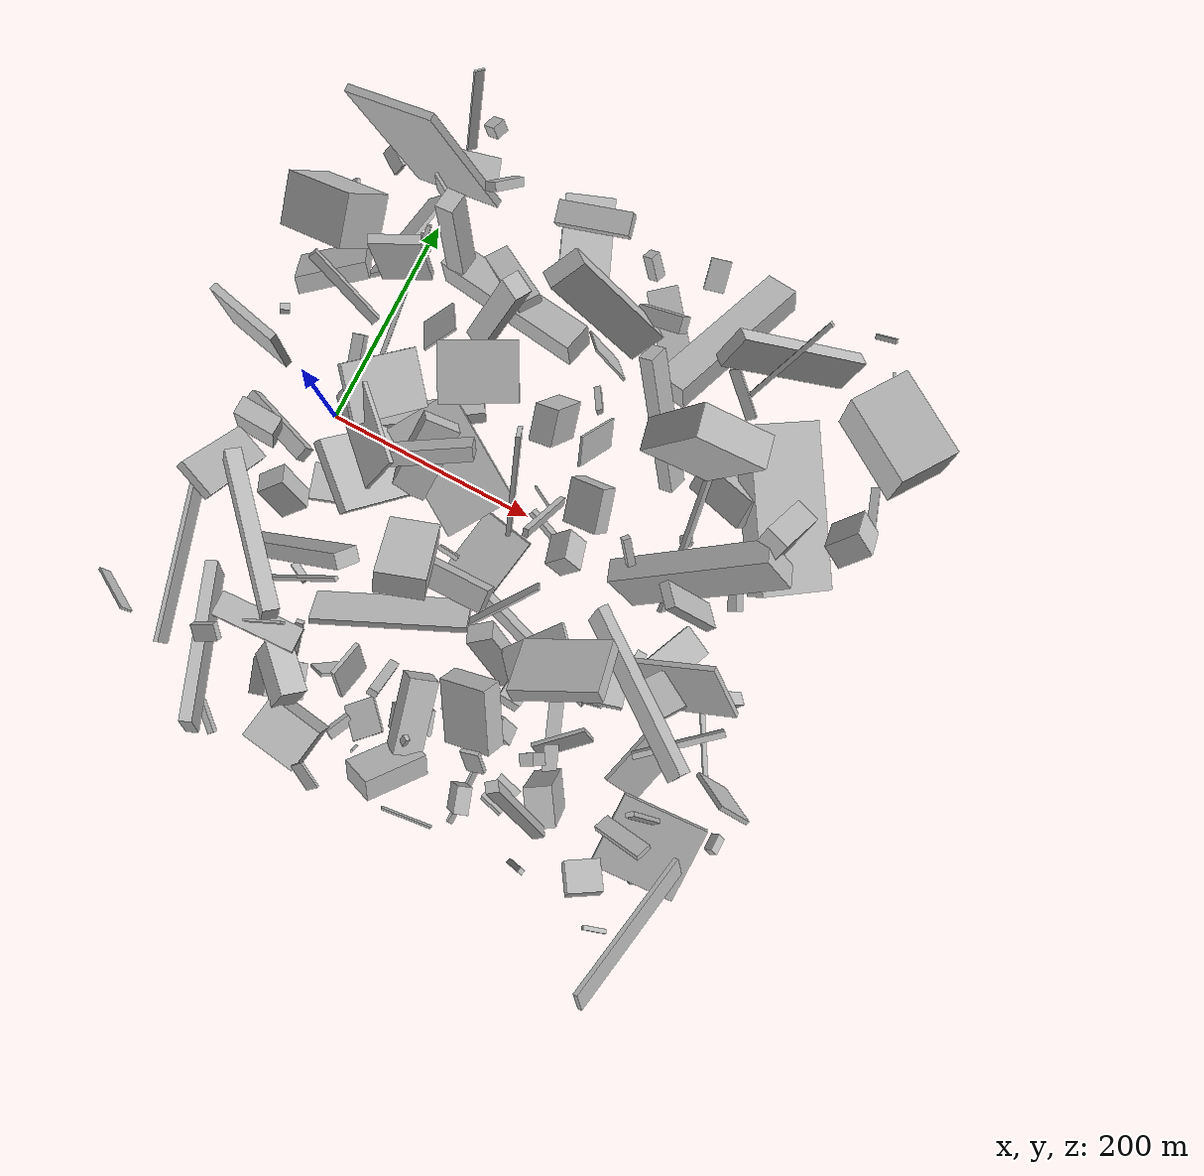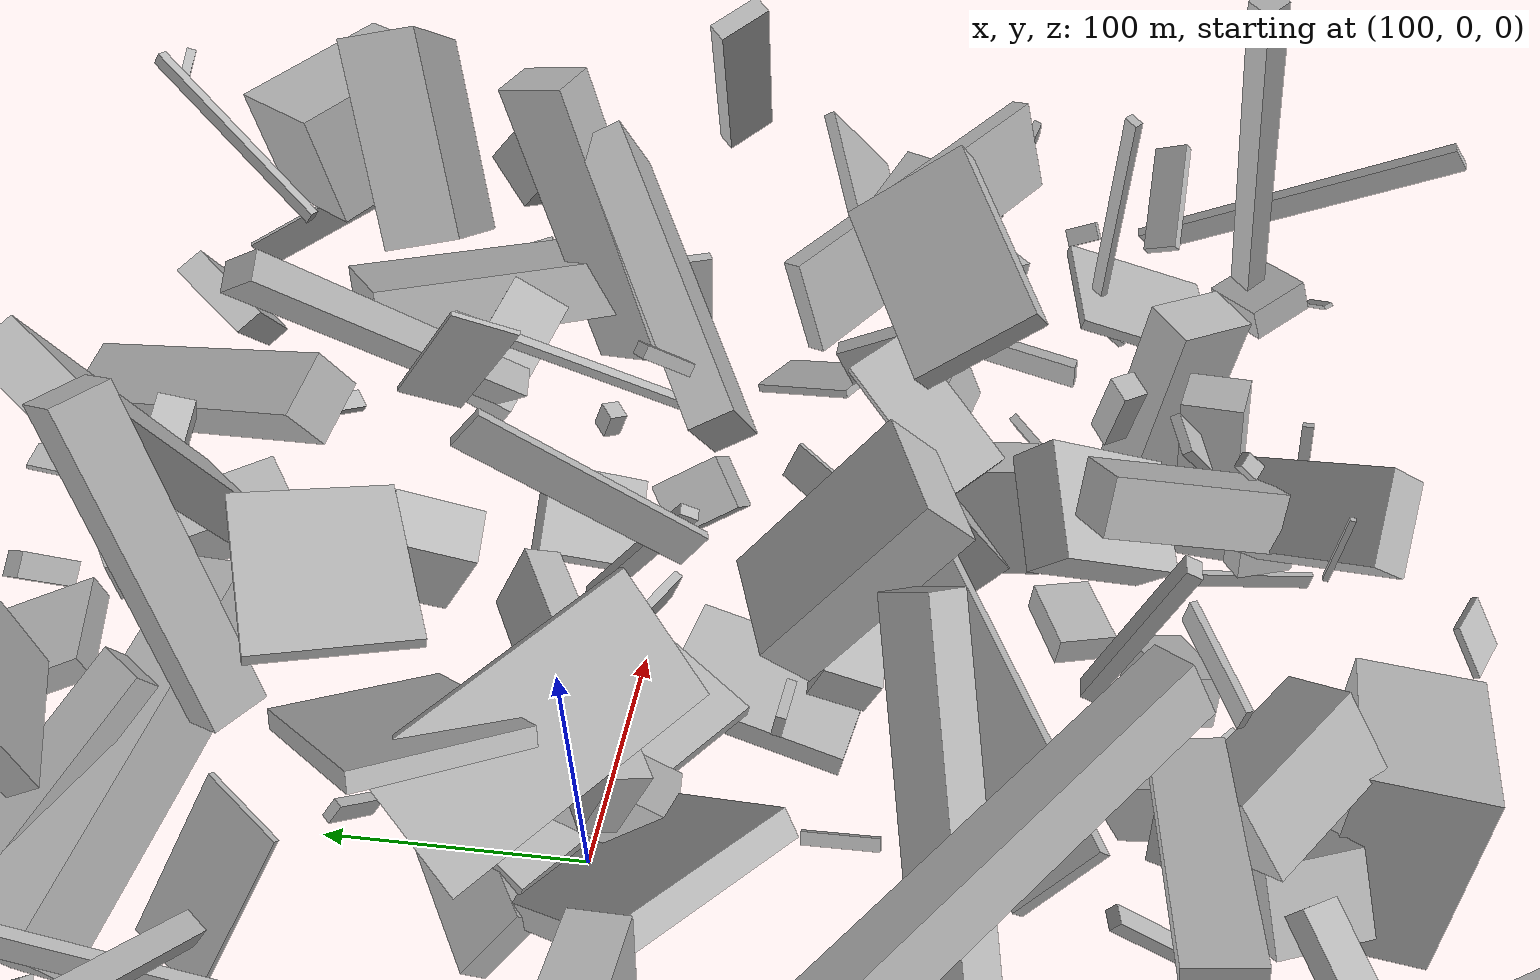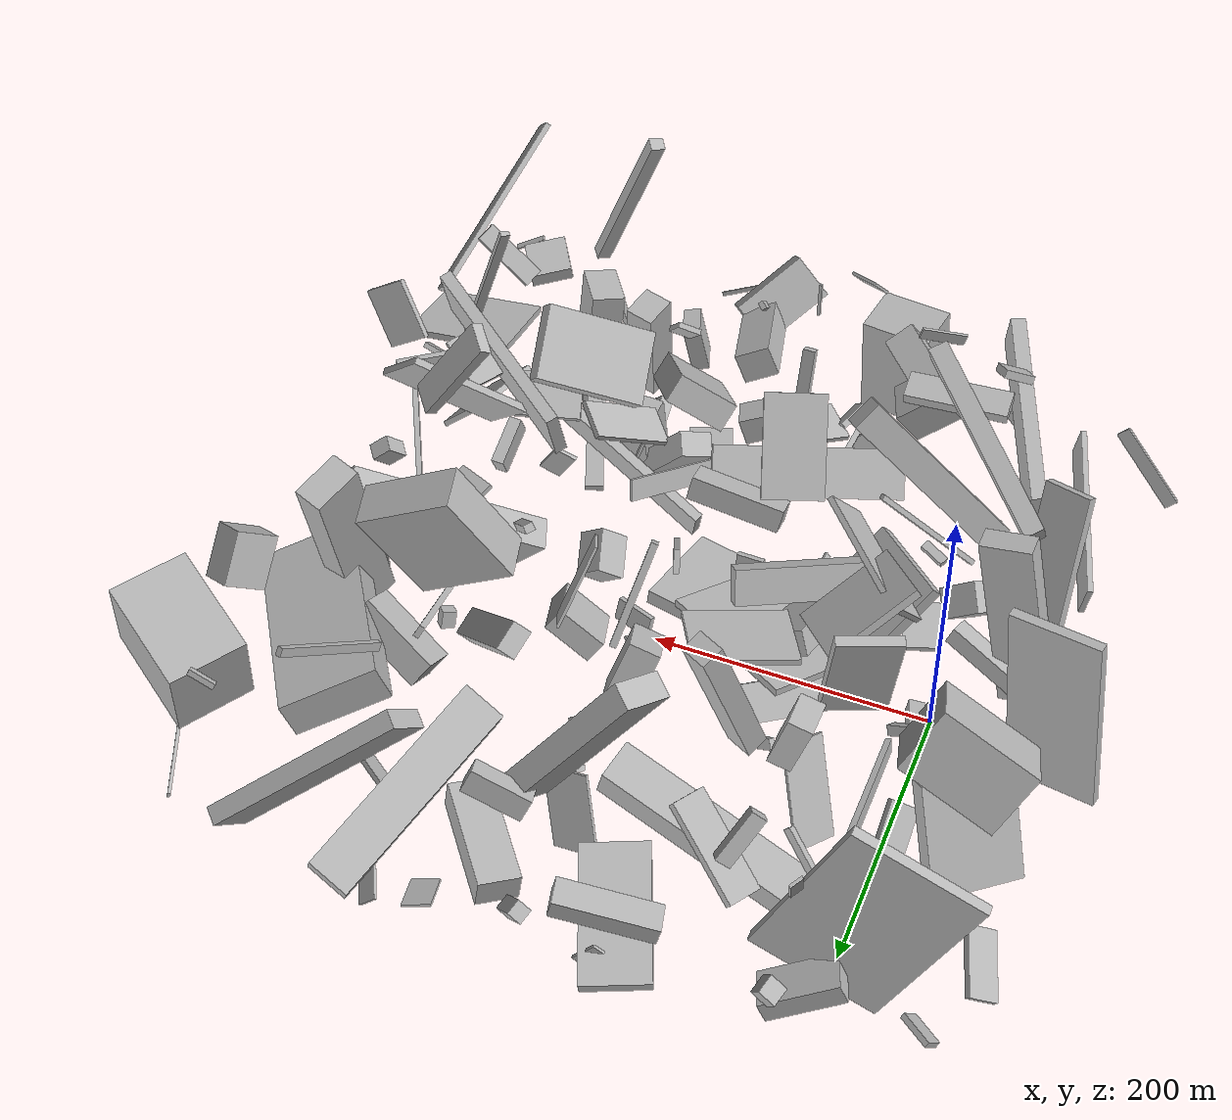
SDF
<sdf version="1.6">
 <world name="default">
  <scene>
   <sky><clouds><speed>12</speed></clouds></sky>
   <ambient>0.4 0.4 0.4 1</ambient>
   <background>0.7 0.7 0.7 1</background>
   <shadows>1</shadows>
  </scene>
  <gravity>0 0 -9.8066</gravity>
  <magnetic_field>6e-06 2.3e-05 -4.2e-05</magnetic_field>
  <physics default="0" name="default_physics" type="ode">
   <ode>
    <solver>
     <type>quick</type>
     <iters>10</iters>
     <sor>1.0</sor>
     <use_dynamic_moi_rescaling>0</use_dynamic_moi_rescaling>
    </solver>
    <constraints>
     <cfm>0</cfm>
     <erp>0.2</erp>
     <contact_max_correcting_vel>100</contact_max_correcting_vel>
     <contact_surface_layer>0.001</contact_surface_layer>
    </constraints>
   </ode>
   <max_step_size>0.004</max_step_size>
   <real_time_factor>1</real_time_factor>
   <real_time_update_rate>250</real_time_update_rate>
  </physics>
  <light name="sun" type="directional">
   <pose>0 0 10 0 0 0</pose>
   <diffuse>0.8 0.8 0.8 1</diffuse>
   <specular>0.2 0.2 0.2 1</specular>
   <attenuation>
    <range>1000</range>
    <constant>0.9</constant>
    <linear>0.01</linear>
    <quadratic>0.001</quadratic>
   </attenuation>
   <direction>-0.5 0.1 -0.9</direction>
  </light>
  <model name="building_1">
   <static>0</static>
   <pose>376.4160862535972 -146.44438053966266 88.0948599853075 -1.4754081273035888 0.10367343675108107 -0.8332753913145137</pose>
   <link name="link">
    <gravity>0</gravity>
    <pose>0 0 40.0 0 0 0</pose>
    <collision name="collision"><geometry><box><size>5 13 80</size></box></geometry></collision>
    <visual name="visual">
     <cast_shadows>0</cast_shadows>
     <geometry><box><size>5 13 80</size></box></geometry>
     <material>
      <script>
       <uri>model://HANNAS_wall/materials/scripts</uri>
       <uri>model://HANNAS_wall/materials/textures</uri>
       <name>vrc/HANNAS_wall</name>
      </script>
     </material>
    </visual>
   </link>
  </model>
  <model name="building_2">
   <static>0</static>
   <pose>321.794513420715 -165.00204097768082 21.678044561745722 -0.9192522268929308 0.3534638589230469 -2.357106813213301</pose>
   <link name="link">
    <gravity>0</gravity>
    <pose>0 0 2.0 0 0 0</pose>
    <collision name="collision"><geometry><box><size>52 20 4</size></box></geometry></collision>
    <visual name="visual">
     <cast_shadows>0</cast_shadows>
     <geometry><box><size>52 20 4</size></box></geometry>
     <material>
      <script>
       <uri>model://HANNAS_wall/materials/scripts</uri>
       <uri>model://HANNAS_wall/materials/textures</uri>
       <name>vrc/HANNAS_wall</name>
      </script>
     </material>
    </visual>
   </link>
  </model>
  <model name="building_3">
   <static>0</static>
   <pose>354.5128607631851 -94.16857466660295 146.5665015767709 -2.9184667837873746 0.1286111085114189 2.4991986860532176</pose>
   <link name="link">
    <gravity>0</gravity>
    <pose>0 0 20.5 0 0 0</pose>
    <collision name="collision"><geometry><box><size>150 9 41</size></box></geometry></collision>
    <visual name="visual">
     <cast_shadows>0</cast_shadows>
     <geometry><box><size>150 9 41</size></box></geometry>
     <material>
      <script>
       <uri>model://HANNAS_wall/materials/scripts</uri>
       <uri>model://HANNAS_wall/materials/textures</uri>
       <name>vrc/HANNAS_wall</name>
      </script>
     </material>
    </visual>
   </link>
  </model>
  <model name="building_4">
   <static>0</static>
   <pose>425.73051805706973 125.45262257571153 39.001884942079954 -0.3493043703149344 1.2353400232045728 -2.9035439773977174</pose>
   <link name="link">
    <gravity>0</gravity>
    <pose>0 0 34.5 0 0 0</pose>
    <collision name="collision"><geometry><box><size>28 150 69</size></box></geometry></collision>
    <visual name="visual">
     <cast_shadows>0</cast_shadows>
     <geometry><box><size>28 150 69</size></box></geometry>
     <material>
      <script>
       <uri>model://HANNAS_wall/materials/scripts</uri>
       <uri>model://HANNAS_wall/materials/textures</uri>
       <name>vrc/HANNAS_wall</name>
      </script>
     </material>
    </visual>
   </link>
  </model>
  <model name="building_5">
   <static>0</static>
   <pose>166.29963931546428 -24.31965193423507 42.806507160785266 1.4587062912754336 0.22575708300513847 -2.1541432712912423</pose>
   <link name="link">
    <gravity>0</gravity>
    <pose>0 0 55.0 0 0 0</pose>
    <collision name="collision"><geometry><box><size>68 5 110</size></box></geometry></collision>
    <visual name="visual">
     <cast_shadows>0</cast_shadows>
     <geometry><box><size>68 5 110</size></box></geometry>
     <material>
      <script>
       <uri>model://HANNAS_wall/materials/scripts</uri>
       <uri>model://HANNAS_wall/materials/textures</uri>
       <name>vrc/HANNAS_wall</name>
      </script>
     </material>
    </visual>
   </link>
  </model>
  <model name="building_6">
   <static>0</static>
   <pose>377.6880837862823 -206.94020165216173 106.07238548488857 0.8250062733947034 0.40075191401996846 1.1423216451960143</pose>
   <link name="link">
    <gravity>0</gravity>
    <pose>0 0 24.5 0 0 0</pose>
    <collision name="collision"><geometry><box><size>15 5 49</size></box></geometry></collision>
    <visual name="visual">
     <cast_shadows>0</cast_shadows>
     <geometry><box><size>15 5 49</size></box></geometry>
     <material>
      <script>
       <uri>model://HANNAS_wall/materials/scripts</uri>
       <uri>model://HANNAS_wall/materials/textures</uri>
       <name>vrc/HANNAS_wall</name>
      </script>
     </material>
    </visual>
   </link>
  </model>
  <model name="building_7">
   <static>0</static>
   <pose>456.1547920603104 -211.42440820597022 65.46820303982317 -0.9627953414029002 0.5830609603476393 -3.0297623825230766</pose>
   <link name="link">
    <gravity>0</gravity>
    <pose>0 0 75.0 0 0 0</pose>
    <collision name="collision"><geometry><box><size>4 21 150</size></box></geometry></collision>
    <visual name="visual">
     <cast_shadows>0</cast_shadows>
     <geometry><box><size>4 21 150</size></box></geometry>
     <material>
      <script>
       <uri>model://HANNAS_wall/materials/scripts</uri>
       <uri>model://HANNAS_wall/materials/textures</uri>
       <name>vrc/HANNAS_wall</name>
      </script>
     </material>
    </visual>
   </link>
  </model>
  <model name="building_8">
   <static>0</static>
   <pose>41.30353054073305 -132.41653340783122 107.94400786044457 -2.607813706330499 -0.8533514266001915 0.25646923328573096</pose>
   <link name="link">
    <gravity>0</gravity>
    <pose>0 0 11.0 0 0 0</pose>
    <collision name="collision"><geometry><box><size>150 14 22</size></box></geometry></collision>
    <visual name="visual">
     <cast_shadows>0</cast_shadows>
     <geometry><box><size>150 14 22</size></box></geometry>
     <material>
      <script>
       <uri>model://HANNAS_wall/materials/scripts</uri>
       <uri>model://HANNAS_wall/materials/textures</uri>
       <name>vrc/HANNAS_wall</name>
      </script>
     </material>
    </visual>
   </link>
  </model>
  <model name="building_9">
   <static>0</static>
   <pose>26.15178590724839 116.82421287293187 147.3940000569861 -0.11068274155271524 -0.0792444836895755 0.4352526490848134</pose>
   <link name="link">
    <gravity>0</gravity>
    <pose>0 0 35.5 0 0 0</pose>
    <collision name="collision"><geometry><box><size>42 8 71</size></box></geometry></collision>
    <visual name="visual">
     <cast_shadows>0</cast_shadows>
     <geometry><box><size>42 8 71</size></box></geometry>
     <material>
      <script>
       <uri>model://HANNAS_wall/materials/scripts</uri>
       <uri>model://HANNAS_wall/materials/textures</uri>
       <name>vrc/HANNAS_wall</name>
      </script>
     </material>
    </visual>
   </link>
  </model>
  <model name="building_10">
   <static>0</static>
   <pose>334.53113471775816 -237.2734280514877 120.0620985600296 -0.3714505349165468 -0.17752430562716387 0.6885574519491108</pose>
   <link name="link">
    <gravity>0</gravity>
    <pose>0 0 75.0 0 0 0</pose>
    <collision name="collision"><geometry><box><size>10 9 150</size></box></geometry></collision>
    <visual name="visual">
     <cast_shadows>0</cast_shadows>
     <geometry><box><size>10 9 150</size></box></geometry>
     <material>
      <script>
       <uri>model://HANNAS_wall/materials/scripts</uri>
       <uri>model://HANNAS_wall/materials/textures</uri>
       <name>vrc/HANNAS_wall</name>
      </script>
     </material>
    </visual>
   </link>
  </model>
  <model name="building_11">
   <static>0</static>
   <pose>239.5860255502816 50.33478420334243 43.24347063263315 2.0564517696885187 -0.6238064918203996 -0.007543712241795957</pose>
   <link name="link">
    <gravity>0</gravity>
    <pose>0 0 21.0 0 0 0</pose>
    <collision name="collision"><geometry><box><size>38 17 42</size></box></geometry></collision>
    <visual name="visual">
     <cast_shadows>0</cast_shadows>
     <geometry><box><size>38 17 42</size></box></geometry>
     <material>
      <script>
       <uri>model://HANNAS_wall/materials/scripts</uri>
       <uri>model://HANNAS_wall/materials/textures</uri>
       <name>vrc/HANNAS_wall</name>
      </script>
     </material>
    </visual>
   </link>
  </model>
  <model name="building_12">
   <static>0</static>
   <pose>-6.520405088961868 -77.17492732994309 29.772876379950986 0.5663911644474068 0.8044364382784117 -0.3394198197569569</pose>
   <link name="link">
    <gravity>0</gravity>
    <pose>0 0 11.0 0 0 0</pose>
    <collision name="collision"><geometry><box><size>38 27 22</size></box></geometry></collision>
    <visual name="visual">
     <cast_shadows>0</cast_shadows>
     <geometry><box><size>38 27 22</size></box></geometry>
     <material>
      <script>
       <uri>model://HANNAS_wall/materials/scripts</uri>
       <uri>model://HANNAS_wall/materials/textures</uri>
       <name>vrc/HANNAS_wall</name>
      </script>
     </material>
    </visual>
   </link>
  </model>
  <model name="building_13">
   <static>0</static>
   <pose>73.87144601459028 -162.85272034467204 54.95055439336721 -1.437825040534785 -0.7685398482779495 -1.2402216918093765</pose>
   <link name="link">
    <gravity>0</gravity>
    <pose>0 0 69.0 0 0 0</pose>
    <collision name="collision"><geometry><box><size>36 6 138</size></box></geometry></collision>
    <visual name="visual">
     <cast_shadows>0</cast_shadows>
     <geometry><box><size>36 6 138</size></box></geometry>
     <material>
      <script>
       <uri>model://HANNAS_wall/materials/scripts</uri>
       <uri>model://HANNAS_wall/materials/textures</uri>
       <name>vrc/HANNAS_wall</name>
      </script>
     </material>
    </visual>
   </link>
  </model>
  <model name="building_14">
   <static>0</static>
   <pose>397.5493779914432 250.81627033285025 160.21853557276663 -2.0722995644752498 0.5127891272918129 -3.081199250161578</pose>
   <link name="link">
    <gravity>0</gravity>
    <pose>0 0 2.0 0 0 0</pose>
    <collision name="collision"><geometry><box><size>18 4 4</size></box></geometry></collision>
    <visual name="visual">
     <cast_shadows>0</cast_shadows>
     <geometry><box><size>18 4 4</size></box></geometry>
     <material>
      <script>
       <uri>model://HANNAS_wall/materials/scripts</uri>
       <uri>model://HANNAS_wall/materials/textures</uri>
       <name>vrc/HANNAS_wall</name>
      </script>
     </material>
    </visual>
   </link>
  </model>
  <model name="building_15">
   <static>0</static>
   <pose>368.0672884585115 -74.57408986795511 27.928470229735865 2.8033595496282184 1.2547871603637337 -2.346654197150561</pose>
   <link name="link">
    <gravity>0</gravity>
    <pose>0 0 26.5 0 0 0</pose>
    <collision name="collision"><geometry><box><size>4 31 53</size></box></geometry></collision>
    <visual name="visual">
     <cast_shadows>0</cast_shadows>
     <geometry><box><size>4 31 53</size></box></geometry>
     <material>
      <script>
       <uri>model://HANNAS_wall/materials/scripts</uri>
       <uri>model://HANNAS_wall/materials/textures</uri>
       <name>vrc/HANNAS_wall</name>
      </script>
     </material>
    </visual>
   </link>
  </model>
  <model name="building_16">
   <static>0</static>
   <pose>76.28044837517167 -228.210252111113 111.75078828439057 2.7163113510513712 -0.9697268860755308 1.1883598263035349</pose>
   <link name="link">
    <gravity>0</gravity>
    <pose>0 0 11.5 0 0 0</pose>
    <collision name="collision"><geometry><box><size>29 49 23</size></box></geometry></collision>
    <visual name="visual">
     <cast_shadows>0</cast_shadows>
     <geometry><box><size>29 49 23</size></box></geometry>
     <material>
      <script>
       <uri>model://HANNAS_wall/materials/scripts</uri>
       <uri>model://HANNAS_wall/materials/textures</uri>
       <name>vrc/HANNAS_wall</name>
      </script>
     </material>
    </visual>
   </link>
  </model>
  <model name="building_17">
   <static>0</static>
   <pose>99.00438028899181 31.581031771062978 74.12906480237689 -2.108115493406043 -0.40126744923971264 -2.984121978935132</pose>
   <link name="link">
    <gravity>0</gravity>
    <pose>0 0 36.5 0 0 0</pose>
    <collision name="collision"><geometry><box><size>33 18 73</size></box></geometry></collision>
    <visual name="visual">
     <cast_shadows>0</cast_shadows>
     <geometry><box><size>33 18 73</size></box></geometry>
     <material>
      <script>
       <uri>model://HANNAS_wall/materials/scripts</uri>
       <uri>model://HANNAS_wall/materials/textures</uri>
       <name>vrc/HANNAS_wall</name>
      </script>
     </material>
    </visual>
   </link>
  </model>
  <model name="building_18">
   <static>0</static>
   <pose>282.1772084327535 220.4235337717805 66.83973698281358 2.8454443593669274 -0.42140982545945116 -0.22067761689370874</pose>
   <link name="link">
    <gravity>0</gravity>
    <pose>0 0 12.0 0 0 0</pose>
    <collision name="collision"><geometry><box><size>31 150 24</size></box></geometry></collision>
    <visual name="visual">
     <cast_shadows>0</cast_shadows>
     <geometry><box><size>31 150 24</size></box></geometry>
     <material>
      <script>
       <uri>model://HANNAS_wall/materials/scripts</uri>
       <uri>model://HANNAS_wall/materials/textures</uri>
       <name>vrc/HANNAS_wall</name>
      </script>
     </material>
    </visual>
   </link>
  </model>
  <model name="building_19">
   <static>0</static>
   <pose>-21.08721508140144 -173.25944725411205 45.36696916930304 1.2660569894729223 0.013864981769873058 0.4083211484136384</pose>
   <link name="link">
    <gravity>0</gravity>
    <pose>0 0 72.5 0 0 0</pose>
    <collision name="collision"><geometry><box><size>11 35 145</size></box></geometry></collision>
    <visual name="visual">
     <cast_shadows>0</cast_shadows>
     <geometry><box><size>11 35 145</size></box></geometry>
     <material>
      <script>
       <uri>model://HANNAS_wall/materials/scripts</uri>
       <uri>model://HANNAS_wall/materials/textures</uri>
       <name>vrc/HANNAS_wall</name>
      </script>
     </material>
    </visual>
   </link>
  </model>
  <model name="building_20">
   <static>0</static>
   <pose>66.04014127446314 237.0900105829487 123.93164978186473 0.6961059481824453 0.4749691082469154 -1.0595801647672962</pose>
   <link name="link">
    <gravity>0</gravity>
    <pose>0 0 18.5 0 0 0</pose>
    <collision name="collision"><geometry><box><size>8 11 37</size></box></geometry></collision>
    <visual name="visual">
     <cast_shadows>0</cast_shadows>
     <geometry><box><size>8 11 37</size></box></geometry>
     <material>
      <script>
       <uri>model://HANNAS_wall/materials/scripts</uri>
       <uri>model://HANNAS_wall/materials/textures</uri>
       <name>vrc/HANNAS_wall</name>
      </script>
     </material>
    </visual>
   </link>
  </model>
  <model name="building_21">
   <static>0</static>
   <pose>172.52710277176084 164.6042790900808 107.5862120504331 1.168915716080449 0.41591956409434117 2.4396420393022553</pose>
   <link name="link">
    <gravity>0</gravity>
    <pose>0 0 17.0 0 0 0</pose>
    <collision name="collision"><geometry><box><size>18 150 34</size></box></geometry></collision>
    <visual name="visual">
     <cast_shadows>0</cast_shadows>
     <geometry><box><size>18 150 34</size></box></geometry>
     <material>
      <script>
       <uri>model://HANNAS_wall/materials/scripts</uri>
       <uri>model://HANNAS_wall/materials/textures</uri>
       <name>vrc/HANNAS_wall</name>
      </script>
     </material>
    </visual>
   </link>
  </model>
  <model name="building_22">
   <static>0</static>
   <pose>334.19656517361005 45.284084830499125 43.795019441487 1.0515724648564015 -0.47713761523601633 1.7474796630396687</pose>
   <link name="link">
    <gravity>0</gravity>
    <pose>0 0 2.0 0 0 0</pose>
    <collision name="collision"><geometry><box><size>150 9 4</size></box></geometry></collision>
    <visual name="visual">
     <cast_shadows>0</cast_shadows>
     <geometry><box><size>150 9 4</size></box></geometry>
     <material>
      <script>
       <uri>model://HANNAS_wall/materials/scripts</uri>
       <uri>model://HANNAS_wall/materials/textures</uri>
       <name>vrc/HANNAS_wall</name>
      </script>
     </material>
    </visual>
   </link>
  </model>
  <model name="building_23">
   <static>0</static>
   <pose>94.46698053730597 76.94010614579932 32.953451613596116 -2.819256314067834 0.6802738318804274 -0.4839969857501051</pose>
   <link name="link">
    <gravity>0</gravity>
    <pose>0 0 4.0 0 0 0</pose>
    <collision name="collision"><geometry><box><size>21 4 8</size></box></geometry></collision>
    <visual name="visual">
     <cast_shadows>0</cast_shadows>
     <geometry><box><size>21 4 8</size></box></geometry>
     <material>
      <script>
       <uri>model://HANNAS_wall/materials/scripts</uri>
       <uri>model://HANNAS_wall/materials/textures</uri>
       <name>vrc/HANNAS_wall</name>
      </script>
     </material>
    </visual>
   </link>
  </model>
  <model name="building_24">
   <static>0</static>
   <pose>-79.30790828153852 158.46115077522464 20.308698644069047 2.090210067299913 -0.7769290529330102 3.0958314756266185</pose>
   <link name="link">
    <gravity>0</gravity>
    <pose>0 0 23.0 0 0 0</pose>
    <collision name="collision"><geometry><box><size>4 26 46</size></box></geometry></collision>
    <visual name="visual">
     <cast_shadows>0</cast_shadows>
     <geometry><box><size>4 26 46</size></box></geometry>
     <material>
      <script>
       <uri>model://HANNAS_wall/materials/scripts</uri>
       <uri>model://HANNAS_wall/materials/textures</uri>
       <name>vrc/HANNAS_wall</name>
      </script>
     </material>
    </visual>
   </link>
  </model>
  <model name="building_25">
   <static>0</static>
   <pose>262.5823089637459 114.27698266590207 104.37753385290335 0.7214123470604827 -0.7723846508493951 2.315140415091539</pose>
   <link name="link">
    <gravity>0</gravity>
    <pose>0 0 6.5 0 0 0</pose>
    <collision name="collision"><geometry><box><size>138 20 13</size></box></geometry></collision>
    <visual name="visual">
     <cast_shadows>0</cast_shadows>
     <geometry><box><size>138 20 13</size></box></geometry>
     <material>
      <script>
       <uri>model://HANNAS_wall/materials/scripts</uri>
       <uri>model://HANNAS_wall/materials/textures</uri>
       <name>vrc/HANNAS_wall</name>
      </script>
     </material>
    </visual>
   </link>
  </model>
  <model name="building_26">
   <static>0</static>
   <pose>389.4513239217106 65.41458707747333 88.47012598348405 1.477942018139635 0.2043180008722151 1.2077549162519823</pose>
   <link name="link">
    <gravity>0</gravity>
    <pose>0 0 11.0 0 0 0</pose>
    <collision name="collision"><geometry><box><size>36 150 22</size></box></geometry></collision>
    <visual name="visual">
     <cast_shadows>0</cast_shadows>
     <geometry><box><size>36 150 22</size></box></geometry>
     <material>
      <script>
       <uri>model://HANNAS_wall/materials/scripts</uri>
       <uri>model://HANNAS_wall/materials/textures</uri>
       <name>vrc/HANNAS_wall</name>
      </script>
     </material>
    </visual>
   </link>
  </model>
  <model name="building_27">
   <static>0</static>
   <pose>226.13529559083128 -131.29157993784813 46.68027398603676 0.9919838998628088 -0.912165656827948 2.7110060163420786</pose>
   <link name="link">
    <gravity>0</gravity>
    <pose>0 0 12.0 0 0 0</pose>
    <collision name="collision"><geometry><box><size>76 18 24</size></box></geometry></collision>
    <visual name="visual">
     <cast_shadows>0</cast_shadows>
     <geometry><box><size>76 18 24</size></box></geometry>
     <material>
      <script>
       <uri>model://HANNAS_wall/materials/scripts</uri>
       <uri>model://HANNAS_wall/materials/textures</uri>
       <name>vrc/HANNAS_wall</name>
      </script>
     </material>
    </visual>
   </link>
  </model>
  <model name="building_28">
   <static>0</static>
   <pose>-52.261825400239495 19.625794024722012 81.91001618558087 1.4669150647686426 0.0011002644229171294 -1.7857085148524698</pose>
   <link name="link">
    <gravity>0</gravity>
    <pose>0 0 32.0 0 0 0</pose>
    <collision name="collision"><geometry><box><size>7 150 64</size></box></geometry></collision>
    <visual name="visual">
     <cast_shadows>0</cast_shadows>
     <geometry><box><size>7 150 64</size></box></geometry>
     <material>
      <script>
       <uri>model://HANNAS_wall/materials/scripts</uri>
       <uri>model://HANNAS_wall/materials/textures</uri>
       <name>vrc/HANNAS_wall</name>
      </script>
     </material>
    </visual>
   </link>
  </model>
  <model name="building_29">
   <static>0</static>
   <pose>-42.3636002411799 146.69179338204282 137.64751133919503 0.5546674425060714 0.47076854257271544 -1.3419680814752857</pose>
   <link name="link">
    <gravity>0</gravity>
    <pose>0 0 23.0 0 0 0</pose>
    <collision name="collision"><geometry><box><size>45 70 46</size></box></geometry></collision>
    <visual name="visual">
     <cast_shadows>0</cast_shadows>
     <geometry><box><size>45 70 46</size></box></geometry>
     <material>
      <script>
       <uri>model://HANNAS_wall/materials/scripts</uri>
       <uri>model://HANNAS_wall/materials/textures</uri>
       <name>vrc/HANNAS_wall</name>
      </script>
     </material>
    </visual>
   </link>
  </model>
  <model name="building_30">
   <static>0</static>
   <pose>123.02762506412898 -198.14306445434735 29.35350856126475 1.2673694231294488 0.3386167151943627 1.3967399124755793</pose>
   <link name="link">
    <gravity>0</gravity>
    <pose>0 0 2.0 0 0 0</pose>
    <collision name="collision"><geometry><box><size>35 48 4</size></box></geometry></collision>
    <visual name="visual">
     <cast_shadows>0</cast_shadows>
     <geometry><box><size>35 48 4</size></box></geometry>
     <material>
      <script>
       <uri>model://HANNAS_wall/materials/scripts</uri>
       <uri>model://HANNAS_wall/materials/textures</uri>
       <name>vrc/HANNAS_wall</name>
      </script>
     </material>
    </visual>
   </link>
  </model>
  <model name="building_31">
   <static>0</static>
   <pose>80.67059904556265 -131.9698000760895 60.571103251553474 -2.506998489690205 -0.46908347773046 2.5199186450086803</pose>
   <link name="link">
    <gravity>0</gravity>
    <pose>0 0 50.5 0 0 0</pose>
    <collision name="collision"><geometry><box><size>4 4 101</size></box></geometry></collision>
    <visual name="visual">
     <cast_shadows>0</cast_shadows>
     <geometry><box><size>4 4 101</size></box></geometry>
     <material>
      <script>
       <uri>model://HANNAS_wall/materials/scripts</uri>
       <uri>model://HANNAS_wall/materials/textures</uri>
       <name>vrc/HANNAS_wall</name>
      </script>
     </material>
    </visual>
   </link>
  </model>
  <model name="building_32">
   <static>0</static>
   <pose>219.72203453452343 -182.26169040566378 52.562105206409456 0.7327746189840624 0.7828629512888013 1.1082799228891282</pose>
   <link name="link">
    <gravity>0</gravity>
    <pose>0 0 23.5 0 0 0</pose>
    <collision name="collision"><geometry><box><size>22 63 47</size></box></geometry></collision>
    <visual name="visual">
     <cast_shadows>0</cast_shadows>
     <geometry><box><size>22 63 47</size></box></geometry>
     <material>
      <script>
       <uri>model://HANNAS_wall/materials/scripts</uri>
       <uri>model://HANNAS_wall/materials/textures</uri>
       <name>vrc/HANNAS_wall</name>
      </script>
     </material>
    </visual>
   </link>
  </model>
  <model name="building_33">
   <static>0</static>
   <pose>56.576184402919324 -28.787532848103098 96.48672555799175 -1.4617217553823434 0.5139827953187076 -0.982608609802457</pose>
   <link name="link">
    <gravity>0</gravity>
    <pose>0 0 47.5 0 0 0</pose>
    <collision name="collision"><geometry><box><size>13 25 95</size></box></geometry></collision>
    <visual name="visual">
     <cast_shadows>0</cast_shadows>
     <geometry><box><size>13 25 95</size></box></geometry>
     <material>
      <script>
       <uri>model://HANNAS_wall/materials/scripts</uri>
       <uri>model://HANNAS_wall/materials/textures</uri>
       <name>vrc/HANNAS_wall</name>
      </script>
     </material>
    </visual>
   </link>
  </model>
  <model name="building_34">
   <static>0</static>
   <pose>64.43402831393007 196.68585581924083 28.339853494502115 0.06470640049518289 -1.0327633727330865 2.4750081207220638</pose>
   <link name="link">
    <gravity>0</gravity>
    <pose>0 0 36.5 0 0 0</pose>
    <collision name="collision"><geometry><box><size>10 23 73</size></box></geometry></collision>
    <visual name="visual">
     <cast_shadows>0</cast_shadows>
     <geometry><box><size>10 23 73</size></box></geometry>
     <material>
      <script>
       <uri>model://HANNAS_wall/materials/scripts</uri>
       <uri>model://HANNAS_wall/materials/textures</uri>
       <name>vrc/HANNAS_wall</name>
      </script>
     </material>
    </visual>
   </link>
  </model>
  <model name="building_35">
   <static>0</static>
   <pose>401.9951829562367 -89.48850503712364 85.27184238683087 0.6508020158846588 -0.4849498169745137 -1.5427788900317136</pose>
   <link name="link">
    <gravity>0</gravity>
    <pose>0 0 32.0 0 0 0</pose>
    <collision name="collision"><geometry><box><size>5 88 64</size></box></geometry></collision>
    <visual name="visual">
     <cast_shadows>0</cast_shadows>
     <geometry><box><size>5 88 64</size></box></geometry>
     <material>
      <script>
       <uri>model://HANNAS_wall/materials/scripts</uri>
       <uri>model://HANNAS_wall/materials/textures</uri>
       <name>vrc/HANNAS_wall</name>
      </script>
     </material>
    </visual>
   </link>
  </model>
  <model name="building_36">
   <static>0</static>
   <pose>431.1159291759136 -245.11354055889097 32.46296030191151 0.2168859287584645 1.2719765623015247 1.8361699198240584</pose>
   <link name="link">
    <gravity>0</gravity>
    <pose>0 0 36.0 0 0 0</pose>
    <collision name="collision"><geometry><box><size>5 79 72</size></box></geometry></collision>
    <visual name="visual">
     <cast_shadows>0</cast_shadows>
     <geometry><box><size>5 79 72</size></box></geometry>
     <material>
      <script>
       <uri>model://HANNAS_wall/materials/scripts</uri>
       <uri>model://HANNAS_wall/materials/textures</uri>
       <name>vrc/HANNAS_wall</name>
      </script>
     </material>
    </visual>
   </link>
  </model>
  <model name="building_37">
   <static>0</static>
   <pose>337.80199023910774 199.92117738417232 154.15688464535904 0.10551003989471384 -0.6725871223936573 1.1674841648281273</pose>
   <link name="link">
    <gravity>0</gravity>
    <pose>0 0 3.0 0 0 0</pose>
    <collision name="collision"><geometry><box><size>92 4 6</size></box></geometry></collision>
    <visual name="visual">
     <cast_shadows>0</cast_shadows>
     <geometry><box><size>92 4 6</size></box></geometry>
     <material>
      <script>
       <uri>model://HANNAS_wall/materials/scripts</uri>
       <uri>model://HANNAS_wall/materials/textures</uri>
       <name>vrc/HANNAS_wall</name>
      </script>
     </material>
    </visual>
   </link>
  </model>
  <model name="building_38">
   <static>0</static>
   <pose>69.71229761751196 -233.9060467844398 51.393012997485016 -0.01229547052070651 0.6540962113990447 0.3411792793053765</pose>
   <link name="link">
    <gravity>0</gravity>
    <pose>0 0 14.0 0 0 0</pose>
    <collision name="collision"><geometry><box><size>38 32 28</size></box></geometry></collision>
    <visual name="visual">
     <cast_shadows>0</cast_shadows>
     <geometry><box><size>38 32 28</size></box></geometry>
     <material>
      <script>
       <uri>model://HANNAS_wall/materials/scripts</uri>
       <uri>model://HANNAS_wall/materials/textures</uri>
       <name>vrc/HANNAS_wall</name>
      </script>
     </material>
    </visual>
   </link>
  </model>
  <model name="building_39">
   <static>0</static>
   <pose>-50.76114627477821 108.16265215551384 50.25185868041362 1.031898963503408 0.04631644439681034 -2.45004476004433</pose>
   <link name="link">
    <gravity>0</gravity>
    <pose>0 0 7.5 0 0 0</pose>
    <collision name="collision"><geometry><box><size>63 79 15</size></box></geometry></collision>
    <visual name="visual">
     <cast_shadows>0</cast_shadows>
     <geometry><box><size>63 79 15</size></box></geometry>
     <material>
      <script>
       <uri>model://HANNAS_wall/materials/scripts</uri>
       <uri>model://HANNAS_wall/materials/textures</uri>
       <name>vrc/HANNAS_wall</name>
      </script>
     </material>
    </visual>
   </link>
  </model>
  <model name="building_40">
   <static>0</static>
   <pose>208.21607410145052 -196.8359088065622 104.31963041390765 -0.5432262630070178 1.1088626042540912 2.8927682375566017</pose>
   <link name="link">
    <gravity>0</gravity>
    <pose>0 0 12.5 0 0 0</pose>
    <collision name="collision"><geometry><box><size>22 66 25</size></box></geometry></collision>
    <visual name="visual">
     <cast_shadows>0</cast_shadows>
     <geometry><box><size>22 66 25</size></box></geometry>
     <material>
      <script>
       <uri>model://HANNAS_wall/materials/scripts</uri>
       <uri>model://HANNAS_wall/materials/textures</uri>
       <name>vrc/HANNAS_wall</name>
      </script>
     </material>
    </visual>
   </link>
  </model>
  <model name="building_41">
   <static>0</static>
   <pose>339.4016158458314 -207.8411635292803 58.82418278144763 2.6195387551232097 -1.4346890549597155 -2.037512713990634</pose>
   <link name="link">
    <gravity>0</gravity>
    <pose>0 0 12.0 0 0 0</pose>
    <collision name="collision"><geometry><box><size>97 35 24</size></box></geometry></collision>
    <visual name="visual">
     <cast_shadows>0</cast_shadows>
     <geometry><box><size>97 35 24</size></box></geometry>
     <material>
      <script>
       <uri>model://HANNAS_wall/materials/scripts</uri>
       <uri>model://HANNAS_wall/materials/textures</uri>
       <name>vrc/HANNAS_wall</name>
      </script>
     </material>
    </visual>
   </link>
  </model>
  <model name="building_42">
   <static>0</static>
   <pose>378.16689863550994 -81.47366042221539 129.883777549265 1.426802749585731 1.0934678244318297 -0.7310783812754642</pose>
   <link name="link">
    <gravity>0</gravity>
    <pose>0 0 15.5 0 0 0</pose>
    <collision name="collision"><geometry><box><size>4 38 31</size></box></geometry></collision>
    <visual name="visual">
     <cast_shadows>0</cast_shadows>
     <geometry><box><size>4 38 31</size></box></geometry>
     <material>
      <script>
       <uri>model://HANNAS_wall/materials/scripts</uri>
       <uri>model://HANNAS_wall/materials/textures</uri>
       <name>vrc/HANNAS_wall</name>
      </script>
     </material>
    </visual>
   </link>
  </model>
  <model name="building_43">
   <static>0</static>
   <pose>171.4734553053448 -77.65599706649971 71.174923315416 2.7615533448560945 1.1581462423929307 1.2293938048437218</pose>
   <link name="link">
    <gravity>0</gravity>
    <pose>0 0 11.0 0 0 0</pose>
    <collision name="collision"><geometry><box><size>17 68 22</size></box></geometry></collision>
    <visual name="visual">
     <cast_shadows>0</cast_shadows>
     <geometry><box><size>17 68 22</size></box></geometry>
     <material>
      <script>
       <uri>model://HANNAS_wall/materials/scripts</uri>
       <uri>model://HANNAS_wall/materials/textures</uri>
       <name>vrc/HANNAS_wall</name>
      </script>
     </material>
    </visual>
   </link>
  </model>
  <model name="building_44">
   <static>0</static>
   <pose>322.8785756632143 104.75058448117969 32.517959939953045 1.0364522494832362 -0.5608713212578262 1.548829056154154</pose>
   <link name="link">
    <gravity>0</gravity>
    <pose>0 0 30.5 0 0 0</pose>
    <collision name="collision"><geometry><box><size>29 21 61</size></box></geometry></collision>
    <visual name="visual">
     <cast_shadows>0</cast_shadows>
     <geometry><box><size>29 21 61</size></box></geometry>
     <material>
      <script>
       <uri>model://HANNAS_wall/materials/scripts</uri>
       <uri>model://HANNAS_wall/materials/textures</uri>
       <name>vrc/HANNAS_wall</name>
      </script>
     </material>
    </visual>
   </link>
  </model>
  <model name="building_45">
   <static>0</static>
   <pose>266.34287215184196 -219.69491062699043 78.30885913953088 0.647088847061912 0.4036301565599312 -2.841310848615049</pose>
   <link name="link">
    <gravity>0</gravity>
    <pose>0 0 13.0 0 0 0</pose>
    <collision name="collision"><geometry><box><size>17 4 26</size></box></geometry></collision>
    <visual name="visual">
     <cast_shadows>0</cast_shadows>
     <geometry><box><size>17 4 26</size></box></geometry>
     <material>
      <script>
       <uri>model://HANNAS_wall/materials/scripts</uri>
       <uri>model://HANNAS_wall/materials/textures</uri>
       <name>vrc/HANNAS_wall</name>
      </script>
     </material>
    </visual>
   </link>
  </model>
  <model name="building_46">
   <static>0</static>
   <pose>88.03080917048545 29.090400976745336 45.72619252838359 3.110208071872393 -0.8890027444257729 2.1998588723996653</pose>
   <link name="link">
    <gravity>0</gravity>
    <pose>0 0 13.5 0 0 0</pose>
    <collision name="collision"><geometry><box><size>11 97 27</size></box></geometry></collision>
    <visual name="visual">
     <cast_shadows>0</cast_shadows>
     <geometry><box><size>11 97 27</size></box></geometry>
     <material>
      <script>
       <uri>model://HANNAS_wall/materials/scripts</uri>
       <uri>model://HANNAS_wall/materials/textures</uri>
       <name>vrc/HANNAS_wall</name>
      </script>
     </material>
    </visual>
   </link>
  </model>
  <model name="building_47">
   <static>0</static>
   <pose>405.29904948028786 -189.8070448667247 102.40829468979092 1.3307468465323518 0.2022390762472017 2.2358647323312844</pose>
   <link name="link">
    <gravity>0</gravity>
    <pose>0 0 3.5 0 0 0</pose>
    <collision name="collision"><geometry><box><size>4 124 7</size></box></geometry></collision>
    <visual name="visual">
     <cast_shadows>0</cast_shadows>
     <geometry><box><size>4 124 7</size></box></geometry>
     <material>
      <script>
       <uri>model://HANNAS_wall/materials/scripts</uri>
       <uri>model://HANNAS_wall/materials/textures</uri>
       <name>vrc/HANNAS_wall</name>
      </script>
     </material>
    </visual>
   </link>
  </model>
  <model name="building_48">
   <static>0</static>
   <pose>47.5664360403844 -182.754247729908 112.25746754621912 1.4350996952252737 0.03219537380437962 0.04291236057411192</pose>
   <link name="link">
    <gravity>0</gravity>
    <pose>0 0 11.0 0 0 0</pose>
    <collision name="collision"><geometry><box><size>74 8 22</size></box></geometry></collision>
    <visual name="visual">
     <cast_shadows>0</cast_shadows>
     <geometry><box><size>74 8 22</size></box></geometry>
     <material>
      <script>
       <uri>model://HANNAS_wall/materials/scripts</uri>
       <uri>model://HANNAS_wall/materials/textures</uri>
       <name>vrc/HANNAS_wall</name>
      </script>
     </material>
    </visual>
   </link>
  </model>
  <model name="building_49">
   <static>0</static>
   <pose>178.5500470559251 -216.48935631171645 27.065074063788543 -1.8798940547057987 0.15693917510596456 -1.2649382148744324</pose>
   <link name="link">
    <gravity>0</gravity>
    <pose>0 0 17.5 0 0 0</pose>
    <collision name="collision"><geometry><box><size>23 21 35</size></box></geometry></collision>
    <visual name="visual">
     <cast_shadows>0</cast_shadows>
     <geometry><box><size>23 21 35</size></box></geometry>
     <material>
      <script>
       <uri>model://HANNAS_wall/materials/scripts</uri>
       <uri>model://HANNAS_wall/materials/textures</uri>
       <name>vrc/HANNAS_wall</name>
      </script>
     </material>
    </visual>
   </link>
  </model>
  <model name="building_50">
   <static>0</static>
   <pose>144.1132150248652 -219.654107264043 9.375919308845015 -1.444747890181324 0.2588278696408259 -2.342876292443623</pose>
   <link name="link">
    <gravity>0</gravity>
    <pose>0 0 16.5 0 0 0</pose>
    <collision name="collision"><geometry><box><size>29 4 33</size></box></geometry></collision>
    <visual name="visual">
     <cast_shadows>0</cast_shadows>
     <geometry><box><size>29 4 33</size></box></geometry>
     <material>
      <script>
       <uri>model://HANNAS_wall/materials/scripts</uri>
       <uri>model://HANNAS_wall/materials/textures</uri>
       <name>vrc/HANNAS_wall</name>
      </script>
     </material>
    </visual>
   </link>
  </model>
  <model name="building_51">
   <static>0</static>
   <pose>392.43423570787127 -149.70862035455582 29.455784644858227 0.16296645516141084 0.8119012657555633 -0.1261879468170689</pose>
   <link name="link">
    <gravity>0</gravity>
    <pose>0 0 2.0 0 0 0</pose>
    <collision name="collision"><geometry><box><size>50 58 4</size></box></geometry></collision>
    <visual name="visual">
     <cast_shadows>0</cast_shadows>
     <geometry><box><size>50 58 4</size></box></geometry>
     <material>
      <script>
       <uri>model://HANNAS_wall/materials/scripts</uri>
       <uri>model://HANNAS_wall/materials/textures</uri>
       <name>vrc/HANNAS_wall</name>
      </script>
     </material>
    </visual>
   </link>
  </model>
  <model name="building_52">
   <static>0</static>
   <pose>446.0597380779745 -134.97897153999878 82.29437542633607 -0.3258031193941431 -0.623008873922761 3.098869413708304</pose>
   <link name="link">
    <gravity>0</gravity>
    <pose>0 0 22.5 0 0 0</pose>
    <collision name="collision"><geometry><box><size>36 4 45</size></box></geometry></collision>
    <visual name="visual">
     <cast_shadows>0</cast_shadows>
     <geometry><box><size>36 4 45</size></box></geometry>
     <material>
      <script>
       <uri>model://HANNAS_wall/materials/scripts</uri>
       <uri>model://HANNAS_wall/materials/textures</uri>
       <name>vrc/HANNAS_wall</name>
      </script>
     </material>
    </visual>
   </link>
  </model>
  <model name="building_53">
   <static>0</static>
   <pose>-51.830810470183096 -90.83838609651667 81.77836136711656 1.1313634903979597 -0.1954666098642272 2.750437122598807</pose>
   <link name="link">
    <gravity>0</gravity>
    <pose>0 0 3.5 0 0 0</pose>
    <collision name="collision"><geometry><box><size>36 119 7</size></box></geometry></collision>
    <visual name="visual">
     <cast_shadows>0</cast_shadows>
     <geometry><box><size>36 119 7</size></box></geometry>
     <material>
      <script>
       <uri>model://HANNAS_wall/materials/scripts</uri>
       <uri>model://HANNAS_wall/materials/textures</uri>
       <name>vrc/HANNAS_wall</name>
      </script>
     </material>
    </visual>
   </link>
  </model>
  <model name="building_54">
   <static>0</static>
   <pose>97.6096311518503 149.86537278041234 38.102786201015306 2.1228322564323543 -1.2393382826170296 2.385586749857466</pose>
   <link name="link">
    <gravity>0</gravity>
    <pose>0 0 14.0 0 0 0</pose>
    <collision name="collision"><geometry><box><size>29 150 28</size></box></geometry></collision>
    <visual name="visual">
     <cast_shadows>0</cast_shadows>
     <geometry><box><size>29 150 28</size></box></geometry>
     <material>
      <script>
       <uri>model://HANNAS_wall/materials/scripts</uri>
       <uri>model://HANNAS_wall/materials/textures</uri>
       <name>vrc/HANNAS_wall</name>
      </script>
     </material>
    </visual>
   </link>
  </model>
  <model name="building_55">
   <static>0</static>
   <pose>217.08167721272972 0.7958986996579709 16.71329624224093 -1.9548325420935795 -0.05778395634298868 2.761235673131003</pose>
   <link name="link">
    <gravity>0</gravity>
    <pose>0 0 2.0 0 0 0</pose>
    <collision name="collision"><geometry><box><size>30 16 4</size></box></geometry></collision>
    <visual name="visual">
     <cast_shadows>0</cast_shadows>
     <geometry><box><size>30 16 4</size></box></geometry>
     <material>
      <script>
       <uri>model://HANNAS_wall/materials/scripts</uri>
       <uri>model://HANNAS_wall/materials/textures</uri>
       <name>vrc/HANNAS_wall</name>
      </script>
     </material>
    </visual>
   </link>
  </model>
  <model name="building_56">
   <static>0</static>
   <pose>305.2661999160035 -234.03345948561497 48.5193642904351 1.623186580596972 -0.11394968980806865 -1.833053454094779</pose>
   <link name="link">
    <gravity>0</gravity>
    <pose>0 0 11.0 0 0 0</pose>
    <collision name="collision"><geometry><box><size>25 84 22</size></box></geometry></collision>
    <visual name="visual">
     <cast_shadows>0</cast_shadows>
     <geometry><box><size>25 84 22</size></box></geometry>
     <material>
      <script>
       <uri>model://HANNAS_wall/materials/scripts</uri>
       <uri>model://HANNAS_wall/materials/textures</uri>
       <name>vrc/HANNAS_wall</name>
      </script>
     </material>
    </visual>
   </link>
  </model>
  <model name="building_57">
   <static>0</static>
   <pose>17.95143649006124 -126.6694606371305 140.09569378610257 0.745349753987204 1.1053633119149389 -1.6667616194537134</pose>
   <link name="link">
    <gravity>0</gravity>
    <pose>0 0 7.0 0 0 0</pose>
    <collision name="collision"><geometry><box><size>18 150 14</size></box></geometry></collision>
    <visual name="visual">
     <cast_shadows>0</cast_shadows>
     <geometry><box><size>18 150 14</size></box></geometry>
     <material>
      <script>
       <uri>model://HANNAS_wall/materials/scripts</uri>
       <uri>model://HANNAS_wall/materials/textures</uri>
       <name>vrc/HANNAS_wall</name>
      </script>
     </material>
    </visual>
   </link>
  </model>
  <model name="building_58">
   <static>0</static>
   <pose>91.80755377472981 -45.76474344731979 50.66419148279789 1.5287415096976253 -0.7023529443411162 -2.2733380345429373</pose>
   <link name="link">
    <gravity>0</gravity>
    <pose>0 0 33.0 0 0 0</pose>
    <collision name="collision"><geometry><box><size>117 10 66</size></box></geometry></collision>
    <visual name="visual">
     <cast_shadows>0</cast_shadows>
     <geometry><box><size>117 10 66</size></box></geometry>
     <material>
      <script>
       <uri>model://HANNAS_wall/materials/scripts</uri>
       <uri>model://HANNAS_wall/materials/textures</uri>
       <name>vrc/HANNAS_wall</name>
      </script>
     </material>
    </visual>
   </link>
  </model>
  <model name="building_59">
   <static>0</static>
   <pose>-55.04227118646406 230.00179857438184 12.287757902532794 1.6337172044305939 -0.7500733432357919 -2.2184087705915774</pose>
   <link name="link">
    <gravity>0</gravity>
    <pose>0 0 12.0 0 0 0</pose>
    <collision name="collision"><geometry><box><size>4 15 24</size></box></geometry></collision>
    <visual name="visual">
     <cast_shadows>0</cast_shadows>
     <geometry><box><size>4 15 24</size></box></geometry>
     <material>
      <script>
       <uri>model://HANNAS_wall/materials/scripts</uri>
       <uri>model://HANNAS_wall/materials/textures</uri>
       <name>vrc/HANNAS_wall</name>
      </script>
     </material>
    </visual>
   </link>
  </model>
  <model name="building_60">
   <static>0</static>
   <pose>183.91305240886794 -55.200346495274765 13.305628056853696 3.1050014948645632 -0.18312175547290524 1.3945916854471165</pose>
   <link name="link">
    <gravity>0</gravity>
    <pose>0 0 5.5 0 0 0</pose>
    <collision name="collision"><geometry><box><size>75 49 11</size></box></geometry></collision>
    <visual name="visual">
     <cast_shadows>0</cast_shadows>
     <geometry><box><size>75 49 11</size></box></geometry>
     <material>
      <script>
       <uri>model://HANNAS_wall/materials/scripts</uri>
       <uri>model://HANNAS_wall/materials/textures</uri>
       <name>vrc/HANNAS_wall</name>
      </script>
     </material>
    </visual>
   </link>
  </model>
  <model name="building_61">
   <static>0</static>
   <pose>270.5190102062255 -247.91761900706388 43.582941829239566 -1.382416214101956 -0.0009890770831055527 1.9011443520921252</pose>
   <link name="link">
    <gravity>0</gravity>
    <pose>0 0 6.5 0 0 0</pose>
    <collision name="collision"><geometry><box><size>24 40 13</size></box></geometry></collision>
    <visual name="visual">
     <cast_shadows>0</cast_shadows>
     <geometry><box><size>24 40 13</size></box></geometry>
     <material>
      <script>
       <uri>model://HANNAS_wall/materials/scripts</uri>
       <uri>model://HANNAS_wall/materials/textures</uri>
       <name>vrc/HANNAS_wall</name>
      </script>
     </material>
    </visual>
   </link>
  </model>
  <model name="building_62">
   <static>0</static>
   <pose>47.940993149849426 27.38662737019972 129.71936036111128 0.31878581547302126 0.47263176509669746 0.8357936180809133</pose>
   <link name="link">
    <gravity>0</gravity>
    <pose>0 0 3.0 0 0 0</pose>
    <collision name="collision"><geometry><box><size>70 51 6</size></box></geometry></collision>
    <visual name="visual">
     <cast_shadows>0</cast_shadows>
     <geometry><box><size>70 51 6</size></box></geometry>
     <material>
      <script>
       <uri>model://HANNAS_wall/materials/scripts</uri>
       <uri>model://HANNAS_wall/materials/textures</uri>
       <name>vrc/HANNAS_wall</name>
      </script>
     </material>
    </visual>
   </link>
  </model>
  <model name="building_63">
   <static>0</static>
   <pose>0.27603358604562267 39.38345398371168 37.73022273186504 2.922388592740561 -0.25412816880336536 1.8461642530014102</pose>
   <link name="link">
    <gravity>0</gravity>
    <pose>0 0 5.0 0 0 0</pose>
    <collision name="collision"><geometry><box><size>66 11 10</size></box></geometry></collision>
    <visual name="visual">
     <cast_shadows>0</cast_shadows>
     <geometry><box><size>66 11 10</size></box></geometry>
     <material>
      <script>
       <uri>model://HANNAS_wall/materials/scripts</uri>
       <uri>model://HANNAS_wall/materials/textures</uri>
       <name>vrc/HANNAS_wall</name>
      </script>
     </material>
    </visual>
   </link>
  </model>
  <model name="building_64">
   <static>0</static>
   <pose>183.19283603012892 10.507377017553559 107.47435644082985 -1.613735651235798 -0.7717459204915526 1.9344699261271578</pose>
   <link name="link">
    <gravity>0</gravity>
    <pose>0 0 2.0 0 0 0</pose>
    <collision name="collision"><geometry><box><size>104 16 4</size></box></geometry></collision>
    <visual name="visual">
     <cast_shadows>0</cast_shadows>
     <geometry><box><size>104 16 4</size></box></geometry>
     <material>
      <script>
       <uri>model://HANNAS_wall/materials/scripts</uri>
       <uri>model://HANNAS_wall/materials/textures</uri>
       <name>vrc/HANNAS_wall</name>
      </script>
     </material>
    </visual>
   </link>
  </model>
  <model name="building_65">
   <static>0</static>
   <pose>301.52865763682723 -184.75275181556137 69.29679601368818 1.5136294423400503 -0.3219227767838976 0.5437487758179212</pose>
   <link name="link">
    <gravity>0</gravity>
    <pose>0 0 5.5 0 0 0</pose>
    <collision name="collision"><geometry><box><size>12 34 11</size></box></geometry></collision>
    <visual name="visual">
     <cast_shadows>0</cast_shadows>
     <geometry><box><size>12 34 11</size></box></geometry>
     <material>
      <script>
       <uri>model://HANNAS_wall/materials/scripts</uri>
       <uri>model://HANNAS_wall/materials/textures</uri>
       <name>vrc/HANNAS_wall</name>
      </script>
     </material>
    </visual>
   </link>
  </model>
  <model name="building_66">
   <static>0</static>
   <pose>-22.802470374030648 229.26125307400028 100.76526924009967 1.5335930164606553 -1.1762662502063221 -3.1071329728821495</pose>
   <link name="link">
    <gravity>0</gravity>
    <pose>0 0 3.5 0 0 0</pose>
    <collision name="collision"><geometry><box><size>150 91 7</size></box></geometry></collision>
    <visual name="visual">
     <cast_shadows>0</cast_shadows>
     <geometry><box><size>150 91 7</size></box></geometry>
     <material>
      <script>
       <uri>model://HANNAS_wall/materials/scripts</uri>
       <uri>model://HANNAS_wall/materials/textures</uri>
       <name>vrc/HANNAS_wall</name>
      </script>
     </material>
    </visual>
   </link>
  </model>
  <model name="building_67">
   <static>0</static>
   <pose>224.22293992743573 -173.05487060261564 13.4698372061135 0.10100348889524295 -0.01822768737906507 0.3372163114139222</pose>
   <link name="link">
    <gravity>0</gravity>
    <pose>0 0 6.0 0 0 0</pose>
    <collision name="collision"><geometry><box><size>32 24 12</size></box></geometry></collision>
    <visual name="visual">
     <cast_shadows>0</cast_shadows>
     <geometry><box><size>32 24 12</size></box></geometry>
     <material>
      <script>
       <uri>model://HANNAS_wall/materials/scripts</uri>
       <uri>model://HANNAS_wall/materials/textures</uri>
       <name>vrc/HANNAS_wall</name>
      </script>
     </material>
    </visual>
   </link>
  </model>
  <model name="building_68">
   <static>0</static>
   <pose>365.6255595671867 114.3019026269535 47.01323274839724 0.12918715122539526 0.15386214781160779 0.25670715581233955</pose>
   <link name="link">
    <gravity>0</gravity>
    <pose>0 0 2.5 0 0 0</pose>
    <collision name="collision"><geometry><box><size>5 62 5</size></box></geometry></collision>
    <visual name="visual">
     <cast_shadows>0</cast_shadows>
     <geometry><box><size>5 62 5</size></box></geometry>
     <material>
      <script>
       <uri>model://HANNAS_wall/materials/scripts</uri>
       <uri>model://HANNAS_wall/materials/textures</uri>
       <name>vrc/HANNAS_wall</name>
      </script>
     </material>
    </visual>
   </link>
  </model>
  <model name="building_69">
   <static>0</static>
   <pose>346.5326583434328 -67.88923092173873 53.21470052508359 1.1331132197455405 -0.046797359631359864 -0.01795701316111149</pose>
   <link name="link">
    <gravity>0</gravity>
    <pose>0 0 17.5 0 0 0</pose>
    <collision name="collision"><geometry><box><size>9 19 35</size></box></geometry></collision>
    <visual name="visual">
     <cast_shadows>0</cast_shadows>
     <geometry><box><size>9 19 35</size></box></geometry>
     <material>
      <script>
       <uri>model://HANNAS_wall/materials/scripts</uri>
       <uri>model://HANNAS_wall/materials/textures</uri>
       <name>vrc/HANNAS_wall</name>
      </script>
     </material>
    </visual>
   </link>
  </model>
  <model name="building_70">
   <static>0</static>
   <pose>133.91808735505276 -258.1740222888629 13.429921654683918 -1.9083124488739125 -0.8024936866048763 -0.18317648938434103</pose>
   <link name="link">
    <gravity>0</gravity>
    <pose>0 0 12.0 0 0 0</pose>
    <collision name="collision"><geometry><box><size>5 11 24</size></box></geometry></collision>
    <visual name="visual">
     <cast_shadows>0</cast_shadows>
     <geometry><box><size>5 11 24</size></box></geometry>
     <material>
      <script>
       <uri>model://HANNAS_wall/materials/scripts</uri>
       <uri>model://HANNAS_wall/materials/textures</uri>
       <name>vrc/HANNAS_wall</name>
      </script>
     </material>
    </visual>
   </link>
  </model>
  <model name="building_71">
   <static>0</static>
   <pose>290.06568496850986 92.69398694091369 141.27137791783647 -0.47172770716903334 -0.1340662526795461 -1.3598042766235359</pose>
   <link name="link">
    <gravity>0</gravity>
    <pose>0 0 39.5 0 0 0</pose>
    <collision name="collision"><geometry><box><size>29 69 79</size></box></geometry></collision>
    <visual name="visual">
     <cast_shadows>0</cast_shadows>
     <geometry><box><size>29 69 79</size></box></geometry>
     <material>
      <script>
       <uri>model://HANNAS_wall/materials/scripts</uri>
       <uri>model://HANNAS_wall/materials/textures</uri>
       <name>vrc/HANNAS_wall</name>
      </script>
     </material>
    </visual>
   </link>
  </model>
  <model name="building_72">
   <static>0</static>
   <pose>261.7511066303697 -100.32388607723306 51.823572893751724 0.9228650157641158 1.1787501308173542 -1.0068943990475434</pose>
   <link name="link">
    <gravity>0</gravity>
    <pose>0 0 3.5 0 0 0</pose>
    <collision name="collision"><geometry><box><size>28 131 7</size></box></geometry></collision>
    <visual name="visual">
     <cast_shadows>0</cast_shadows>
     <geometry><box><size>28 131 7</size></box></geometry>
     <material>
      <script>
       <uri>model://HANNAS_wall/materials/scripts</uri>
       <uri>model://HANNAS_wall/materials/textures</uri>
       <name>vrc/HANNAS_wall</name>
      </script>
     </material>
    </visual>
   </link>
  </model>
  <model name="building_73">
   <static>0</static>
   <pose>274.3391537275477 -119.04870734641281 93.04128398929625 -1.8715581482691634 -0.556668710674121 0.8820003971549608</pose>
   <link name="link">
    <gravity>0</gravity>
    <pose>0 0 15.0 0 0 0</pose>
    <collision name="collision"><geometry><box><size>66 4 30</size></box></geometry></collision>
    <visual name="visual">
     <cast_shadows>0</cast_shadows>
     <geometry><box><size>66 4 30</size></box></geometry>
     <material>
      <script>
       <uri>model://HANNAS_wall/materials/scripts</uri>
       <uri>model://HANNAS_wall/materials/textures</uri>
       <name>vrc/HANNAS_wall</name>
      </script>
     </material>
    </visual>
   </link>
  </model>
  <model name="building_74">
   <static>0</static>
   <pose>-76.59958676292482 60.243764010496086 55.14996945302295 -2.4910583361628036 -0.17673668917765184 -2.6328666020113607</pose>
   <link name="link">
    <gravity>0</gravity>
    <pose>0 0 2.5 0 0 0</pose>
    <collision name="collision"><geometry><box><size>9 9 5</size></box></geometry></collision>
    <visual name="visual">
     <cast_shadows>0</cast_shadows>
     <geometry><box><size>9 9 5</size></box></geometry>
     <material>
      <script>
       <uri>model://HANNAS_wall/materials/scripts</uri>
       <uri>model://HANNAS_wall/materials/textures</uri>
       <name>vrc/HANNAS_wall</name>
      </script>
     </material>
    </visual>
   </link>
  </model>
  <model name="building_75">
   <static>0</static>
   <pose>400.6250222052582 -249.1896351456278 75.7751723026611 1.422178347306543 -0.33498823862966004 -0.9894152875171716</pose>
   <link name="link">
    <gravity>0</gravity>
    <pose>0 0 15.5 0 0 0</pose>
    <collision name="collision"><geometry><box><size>28 15 31</size></box></geometry></collision>
    <visual name="visual">
     <cast_shadows>0</cast_shadows>
     <geometry><box><size>28 15 31</size></box></geometry>
     <material>
      <script>
       <uri>model://HANNAS_wall/materials/scripts</uri>
       <uri>model://HANNAS_wall/materials/textures</uri>
       <name>vrc/HANNAS_wall</name>
      </script>
     </material>
    </visual>
   </link>
  </model>
  <model name="building_76">
   <static>0</static>
   <pose>243.30392546663643 -4.512868770223961 44.895020606148734 -0.978520477591614 -0.6677831318220884 3.0133410261375224</pose>
   <link name="link">
    <gravity>0</gravity>
    <pose>0 0 15.0 0 0 0</pose>
    <collision name="collision"><geometry><box><size>22 23 30</size></box></geometry></collision>
    <visual name="visual">
     <cast_shadows>0</cast_shadows>
     <geometry><box><size>22 23 30</size></box></geometry>
     <material>
      <script>
       <uri>model://HANNAS_wall/materials/scripts</uri>
       <uri>model://HANNAS_wall/materials/textures</uri>
       <name>vrc/HANNAS_wall</name>
      </script>
     </material>
    </visual>
   </link>
  </model>
  <model name="building_77">
   <static>0</static>
   <pose>304.4059210281267 203.70113577912582 29.414241709882358 2.130036267905826 0.9726261633959762 1.3404312713316233</pose>
   <link name="link">
    <gravity>0</gravity>
    <pose>0 0 24.5 0 0 0</pose>
    <collision name="collision"><geometry><box><size>4 10 49</size></box></geometry></collision>
    <visual name="visual">
     <cast_shadows>0</cast_shadows>
     <geometry><box><size>4 10 49</size></box></geometry>
     <material>
      <script>
       <uri>model://HANNAS_wall/materials/scripts</uri>
       <uri>model://HANNAS_wall/materials/textures</uri>
       <name>vrc/HANNAS_wall</name>
      </script>
     </material>
    </visual>
   </link>
  </model>
  <model name="building_78">
   <static>0</static>
   <pose>284.10958207682023 -92.79382919673753 29.557154874589422 -1.654978099836488 0.02243850558865393 -2.771170967438211</pose>
   <link name="link">
    <gravity>0</gravity>
    <pose>0 0 75.0 0 0 0</pose>
    <collision name="collision"><geometry><box><size>13 4 150</size></box></geometry></collision>
    <visual name="visual">
     <cast_shadows>0</cast_shadows>
     <geometry><box><size>13 4 150</size></box></geometry>
     <material>
      <script>
       <uri>model://HANNAS_wall/materials/scripts</uri>
       <uri>model://HANNAS_wall/materials/textures</uri>
       <name>vrc/HANNAS_wall</name>
      </script>
     </material>
    </visual>
   </link>
  </model>
  <model name="building_79">
   <static>0</static>
   <pose>274.1879529234945 -141.86173981418312 42.276795607848264 1.4237062831154985 1.4327764275156563 -1.781329783606698</pose>
   <link name="link">
    <gravity>0</gravity>
    <pose>0 0 10.0 0 0 0</pose>
    <collision name="collision"><geometry><box><size>55 34 20</size></box></geometry></collision>
    <visual name="visual">
     <cast_shadows>0</cast_shadows>
     <geometry><box><size>55 34 20</size></box></geometry>
     <material>
      <script>
       <uri>model://HANNAS_wall/materials/scripts</uri>
       <uri>model://HANNAS_wall/materials/textures</uri>
       <name>vrc/HANNAS_wall</name>
      </script>
     </material>
    </visual>
   </link>
  </model>
  <model name="building_80">
   <static>0</static>
   <pose>129.59197346512863 267.17886244248314 64.6789226199824 1.9787326182755527 1.3146951737090589 0.6404173915037223</pose>
   <link name="link">
    <gravity>0</gravity>
    <pose>0 0 10.5 0 0 0</pose>
    <collision name="collision"><geometry><box><size>13 69 21</size></box></geometry></collision>
    <visual name="visual">
     <cast_shadows>0</cast_shadows>
     <geometry><box><size>13 69 21</size></box></geometry>
     <material>
      <script>
       <uri>model://HANNAS_wall/materials/scripts</uri>
       <uri>model://HANNAS_wall/materials/textures</uri>
       <name>vrc/HANNAS_wall</name>
      </script>
     </material>
    </visual>
   </link>
  </model>
  <model name="building_81">
   <static>0</static>
   <pose>144.02848465362948 -63.71839156855075 32.82139499330398 -1.8999803328778384 -1.360740939728252 -1.3240492769332304</pose>
   <link name="link">
    <gravity>0</gravity>
    <pose>0 0 10.0 0 0 0</pose>
    <collision name="collision"><geometry><box><size>10 4 20</size></box></geometry></collision>
    <visual name="visual">
     <cast_shadows>0</cast_shadows>
     <geometry><box><size>10 4 20</size></box></geometry>
     <material>
      <script>
       <uri>model://HANNAS_wall/materials/scripts</uri>
       <uri>model://HANNAS_wall/materials/textures</uri>
       <name>vrc/HANNAS_wall</name>
      </script>
     </material>
    </visual>
   </link>
  </model>
  <model name="building_82">
   <static>0</static>
   <pose>427.83939303059634 -103.86104218992648 32.33669988627288 -1.6578252255497208 -0.5292868674641596 -1.1220971624009868</pose>
   <link name="link">
    <gravity>0</gravity>
    <pose>0 0 2.0 0 0 0</pose>
    <collision name="collision"><geometry><box><size>84 4 4</size></box></geometry></collision>
    <visual name="visual">
     <cast_shadows>0</cast_shadows>
     <geometry><box><size>84 4 4</size></box></geometry>
     <material>
      <script>
       <uri>model://HANNAS_wall/materials/scripts</uri>
       <uri>model://HANNAS_wall/materials/textures</uri>
       <name>vrc/HANNAS_wall</name>
      </script>
     </material>
    </visual>
   </link>
  </model>
  <model name="building_83">
   <static>0</static>
   <pose>432.1510319201117 -244.29890692329386 7.896499653876186 -0.24949355145050797 -0.7691261145406426 -2.7520125231913575</pose>
   <link name="link">
    <gravity>0</gravity>
    <pose>0 0 2.0 0 0 0</pose>
    <collision name="collision"><geometry><box><size>4 10 4</size></box></geometry></collision>
    <visual name="visual">
     <cast_shadows>0</cast_shadows>
     <geometry><box><size>4 10 4</size></box></geometry>
     <material>
      <script>
       <uri>model://HANNAS_wall/materials/scripts</uri>
       <uri>model://HANNAS_wall/materials/textures</uri>
       <name>vrc/HANNAS_wall</name>
      </script>
     </material>
    </visual>
   </link>
  </model>
  <model name="building_84">
   <static>0</static>
   <pose>373.2965070279097 -19.650410859970272 156.098569855271 0.3572878815529148 0.4475234770993512 -2.293039086330735</pose>
   <link name="link">
    <gravity>0</gravity>
    <pose>0 0 39.5 0 0 0</pose>
    <collision name="collision"><geometry><box><size>8 22 79</size></box></geometry></collision>
    <visual name="visual">
     <cast_shadows>0</cast_shadows>
     <geometry><box><size>8 22 79</size></box></geometry>
     <material>
      <script>
       <uri>model://HANNAS_wall/materials/scripts</uri>
       <uri>model://HANNAS_wall/materials/textures</uri>
       <name>vrc/HANNAS_wall</name>
      </script>
     </material>
    </visual>
   </link>
  </model>
  <model name="building_85">
   <static>0</static>
   <pose>111.11859087297219 233.7965404278355 37.21217346216281 1.7480087075165385 -1.3319810256660958 1.7739560514399262</pose>
   <link name="link">
    <gravity>0</gravity>
    <pose>0 0 23.0 0 0 0</pose>
    <collision name="collision"><geometry><box><size>11 93 46</size></box></geometry></collision>
    <visual name="visual">
     <cast_shadows>0</cast_shadows>
     <geometry><box><size>11 93 46</size></box></geometry>
     <material>
      <script>
       <uri>model://HANNAS_wall/materials/scripts</uri>
       <uri>model://HANNAS_wall/materials/textures</uri>
       <name>vrc/HANNAS_wall</name>
      </script>
     </material>
    </visual>
   </link>
  </model>
  <model name="building_86">
   <static>0</static>
   <pose>10.68651113254453 110.84368282088225 49.05758865347526 -1.8930632551643003 -1.1323546081305704 -1.1468011343660807</pose>
   <link name="link">
    <gravity>0</gravity>
    <pose>0 0 2.0 0 0 0</pose>
    <collision name="collision"><geometry><box><size>10 150 4</size></box></geometry></collision>
    <visual name="visual">
     <cast_shadows>0</cast_shadows>
     <geometry><box><size>10 150 4</size></box></geometry>
     <material>
      <script>
       <uri>model://HANNAS_wall/materials/scripts</uri>
       <uri>model://HANNAS_wall/materials/textures</uri>
       <name>vrc/HANNAS_wall</name>
      </script>
     </material>
    </visual>
   </link>
  </model>
  <model name="building_87">
   <static>0</static>
   <pose>359.51175408979566 7.2622122835860665 85.90898418541258 2.165101479089315 -0.8668462215504086 2.9838635050032445</pose>
   <link name="link">
    <gravity>0</gravity>
    <pose>0 0 11.0 0 0 0</pose>
    <collision name="collision"><geometry><box><size>49 150 22</size></box></geometry></collision>
    <visual name="visual">
     <cast_shadows>0</cast_shadows>
     <geometry><box><size>49 150 22</size></box></geometry>
     <material>
      <script>
       <uri>model://HANNAS_wall/materials/scripts</uri>
       <uri>model://HANNAS_wall/materials/textures</uri>
       <name>vrc/HANNAS_wall</name>
      </script>
     </material>
    </visual>
   </link>
  </model>
  <model name="building_88">
   <static>0</static>
   <pose>-55.522958240046215 -182.3387185676772 38.78886397275471 -0.1850254326549465 1.4135359113547836 0.10400236901937494</pose>
   <link name="link">
    <gravity>0</gravity>
    <pose>0 0 2.0 0 0 0</pose>
    <collision name="collision"><geometry><box><size>23 150 4</size></box></geometry></collision>
    <visual name="visual">
     <cast_shadows>0</cast_shadows>
     <geometry><box><size>23 150 4</size></box></geometry>
     <material>
      <script>
       <uri>model://HANNAS_wall/materials/scripts</uri>
       <uri>model://HANNAS_wall/materials/textures</uri>
       <name>vrc/HANNAS_wall</name>
      </script>
     </material>
    </visual>
   </link>
  </model>
  <model name="building_89">
   <static>0</static>
   <pose>-58.30412805358293 -43.96439316985135 79.3202683654745 3.0833069885523887 -1.3800195889521174 0.03392743028743543</pose>
   <link name="link">
    <gravity>0</gravity>
    <pose>0 0 18.0 0 0 0</pose>
    <collision name="collision"><geometry><box><size>150 16 36</size></box></geometry></collision>
    <visual name="visual">
     <cast_shadows>0</cast_shadows>
     <geometry><box><size>150 16 36</size></box></geometry>
     <material>
      <script>
       <uri>model://HANNAS_wall/materials/scripts</uri>
       <uri>model://HANNAS_wall/materials/textures</uri>
       <name>vrc/HANNAS_wall</name>
      </script>
     </material>
    </visual>
   </link>
  </model>
  <model name="building_90">
   <static>0</static>
   <pose>112.66291486619494 76.29605529590627 125.10975455780742 -0.2379373086664046 0.10487400609046299 -2.6722480220806903</pose>
   <link name="link">
    <gravity>0</gravity>
    <pose>0 0 2.0 0 0 0</pose>
    <collision name="collision"><geometry><box><size>69 53 4</size></box></geometry></collision>
    <visual name="visual">
     <cast_shadows>0</cast_shadows>
     <geometry><box><size>69 53 4</size></box></geometry>
     <material>
      <script>
       <uri>model://HANNAS_wall/materials/scripts</uri>
       <uri>model://HANNAS_wall/materials/textures</uri>
       <name>vrc/HANNAS_wall</name>
      </script>
     </material>
    </visual>
   </link>
  </model>
  <model name="building_91">
   <static>0</static>
   <pose>174.58085471294916 78.34975745129786 63.327252066702705 1.1916508901984506 -0.45658867915406215 1.8372943687780499</pose>
   <link name="link">
    <gravity>0</gravity>
    <pose>0 0 11.0 0 0 0</pose>
    <collision name="collision"><geometry><box><size>34 46 22</size></box></geometry></collision>
    <visual name="visual">
     <cast_shadows>0</cast_shadows>
     <geometry><box><size>34 46 22</size></box></geometry>
     <material>
      <script>
       <uri>model://HANNAS_wall/materials/scripts</uri>
       <uri>model://HANNAS_wall/materials/textures</uri>
       <name>vrc/HANNAS_wall</name>
      </script>
     </material>
    </visual>
   </link>
  </model>
  <model name="building_92">
   <static>0</static>
   <pose>83.85068176991481 -41.065824067391816 143.31967793542333 1.8390578113786242 -0.6218704499586006 -2.486151966748341</pose>
   <link name="link">
    <gravity>0</gravity>
    <pose>0 0 44.0 0 0 0</pose>
    <collision name="collision"><geometry><box><size>4 45 88</size></box></geometry></collision>
    <visual name="visual">
     <cast_shadows>0</cast_shadows>
     <geometry><box><size>4 45 88</size></box></geometry>
     <material>
      <script>
       <uri>model://HANNAS_wall/materials/scripts</uri>
       <uri>model://HANNAS_wall/materials/textures</uri>
       <name>vrc/HANNAS_wall</name>
      </script>
     </material>
    </visual>
   </link>
  </model>
  <model name="building_93">
   <static>0</static>
   <pose>434.0822830619727 172.53262457157416 111.87162375580719 -1.798561688616774 1.4173238806236899 -0.8266420701996762</pose>
   <link name="link">
    <gravity>0</gravity>
    <pose>0 0 27.0 0 0 0</pose>
    <collision name="collision"><geometry><box><size>57 81 54</size></box></geometry></collision>
    <visual name="visual">
     <cast_shadows>0</cast_shadows>
     <geometry><box><size>57 81 54</size></box></geometry>
     <material>
      <script>
       <uri>model://HANNAS_wall/materials/scripts</uri>
       <uri>model://HANNAS_wall/materials/textures</uri>
       <name>vrc/HANNAS_wall</name>
      </script>
     </material>
    </visual>
   </link>
  </model>
  <model name="building_94">
   <static>0</static>
   <pose>136.92139772007155 -96.64478975827387 125.38126975950084 0.0025765050675883474 -0.7915630665965652 -1.2450400455712047</pose>
   <link name="link">
    <gravity>0</gravity>
    <pose>0 0 11.0 0 0 0</pose>
    <collision name="collision"><geometry><box><size>72 43 22</size></box></geometry></collision>
    <visual name="visual">
     <cast_shadows>0</cast_shadows>
     <geometry><box><size>72 43 22</size></box></geometry>
     <material>
      <script>
       <uri>model://HANNAS_wall/materials/scripts</uri>
       <uri>model://HANNAS_wall/materials/textures</uri>
       <name>vrc/HANNAS_wall</name>
      </script>
     </material>
    </visual>
   </link>
  </model>
  <model name="building_95">
   <static>0</static>
   <pose>349.14385057659933 221.65421346148173 67.29164655759257 -2.1903274456312776 -0.7813215901395121 1.2609877548077126</pose>
   <link name="link">
    <gravity>0</gravity>
    <pose>0 0 6.5 0 0 0</pose>
    <collision name="collision"><geometry><box><size>35 150 13</size></box></geometry></collision>
    <visual name="visual">
     <cast_shadows>0</cast_shadows>
     <geometry><box><size>35 150 13</size></box></geometry>
     <material>
      <script>
       <uri>model://HANNAS_wall/materials/scripts</uri>
       <uri>model://HANNAS_wall/materials/textures</uri>
       <name>vrc/HANNAS_wall</name>
      </script>
     </material>
    </visual>
   </link>
  </model>
  <model name="building_96">
   <static>0</static>
   <pose>159.7985385702707 -184.90714211650027 83.80276856939912 3.0403443130573073 -1.171514466473433 -1.5342305234087912</pose>
   <link name="link">
    <gravity>0</gravity>
    <pose>0 0 3.0 0 0 0</pose>
    <collision name="collision"><geometry><box><size>69 9 6</size></box></geometry></collision>
    <visual name="visual">
     <cast_shadows>0</cast_shadows>
     <geometry><box><size>69 9 6</size></box></geometry>
     <material>
      <script>
       <uri>model://HANNAS_wall/materials/scripts</uri>
       <uri>model://HANNAS_wall/materials/textures</uri>
       <name>vrc/HANNAS_wall</name>
      </script>
     </material>
    </visual>
   </link>
  </model>
  <model name="building_97">
   <static>0</static>
   <pose>93.55366772586504 112.60014380282873 76.39475537278548 0.054137567042516224 0.3015956550707253 1.0948597075324833</pose>
   <link name="link">
    <gravity>0</gravity>
    <pose>0 0 59.0 0 0 0</pose>
    <collision name="collision"><geometry><box><size>16 20 118</size></box></geometry></collision>
    <visual name="visual">
     <cast_shadows>0</cast_shadows>
     <geometry><box><size>16 20 118</size></box></geometry>
     <material>
      <script>
       <uri>model://HANNAS_wall/materials/scripts</uri>
       <uri>model://HANNAS_wall/materials/textures</uri>
       <name>vrc/HANNAS_wall</name>
      </script>
     </material>
    </visual>
   </link>
  </model>
  <model name="building_98">
   <static>0</static>
   <pose>467.8457935260154 97.55473279201911 87.36399042787112 -1.1340136148016968 -0.6174018010687264 0.8570916206182572</pose>
   <link name="link">
    <gravity>0</gravity>
    <pose>0 0 12.0 0 0 0</pose>
    <collision name="collision"><geometry><box><size>32 38 24</size></box></geometry></collision>
    <visual name="visual">
     <cast_shadows>0</cast_shadows>
     <geometry><box><size>32 38 24</size></box></geometry>
     <material>
      <script>
       <uri>model://HANNAS_wall/materials/scripts</uri>
       <uri>model://HANNAS_wall/materials/textures</uri>
       <name>vrc/HANNAS_wall</name>
      </script>
     </material>
    </visual>
   </link>
  </model>
  <model name="building_99">
   <static>0</static>
   <pose>-4.663628454689877 177.8181699060371 45.29006187751745 2.4306716265340675 0.6258661739767227 -0.4876939482275105</pose>
   <link name="link">
    <gravity>0</gravity>
    <pose>0 0 11.5 0 0 0</pose>
    <collision name="collision"><geometry><box><size>4 123 23</size></box></geometry></collision>
    <visual name="visual">
     <cast_shadows>0</cast_shadows>
     <geometry><box><size>4 123 23</size></box></geometry>
     <material>
      <script>
       <uri>model://HANNAS_wall/materials/scripts</uri>
       <uri>model://HANNAS_wall/materials/textures</uri>
       <name>vrc/HANNAS_wall</name>
      </script>
     </material>
    </visual>
   </link>
  </model>
  <model name="building_100">
   <static>0</static>
   <pose>-0.6729483679253239 166.42597410543553 22.648900615441477 -2.1986958300483175 -0.967865795711943 1.5395733910052551</pose>
   <link name="link">
    <gravity>0</gravity>
    <pose>0 0 10.5 0 0 0</pose>
    <collision name="collision"><geometry><box><size>7 25 21</size></box></geometry></collision>
    <visual name="visual">
     <cast_shadows>0</cast_shadows>
     <geometry><box><size>7 25 21</size></box></geometry>
     <material>
      <script>
       <uri>model://HANNAS_wall/materials/scripts</uri>
       <uri>model://HANNAS_wall/materials/textures</uri>
       <name>vrc/HANNAS_wall</name>
      </script>
     </material>
    </visual>
   </link>
  </model>
  <model name="building_101">
   <static>0</static>
   <pose>267.20770520478004 -250.0516005664052 12.26410336552712 1.9546295037365746 -0.07900097407731528 -1.5561285095093795</pose>
   <link name="link">
    <gravity>0</gravity>
    <pose>0 0 1.0 0 0 0</pose>
    <collision name="collision"><geometry><box><size>53 12 2</size></box></geometry></collision>
    <visual name="visual">
     <cast_shadows>0</cast_shadows>
     <geometry><box><size>53 12 2</size></box></geometry>
     <material>
      <script>
       <uri>model://HANNAS_wall/materials/scripts</uri>
       <uri>model://HANNAS_wall/materials/textures</uri>
       <name>vrc/HANNAS_wall</name>
      </script>
     </material>
    </visual>
   </link>
  </model>
  <model name="building_102">
   <static>0</static>
   <pose>168.03374756978437 -247.47713750630282 119.3058316439384 -1.864695157224409 -1.4699283951301598 -1.4267439228362921</pose>
   <link name="link">
    <gravity>0</gravity>
    <pose>0 0 1.0 0 0 0</pose>
    <collision name="collision"><geometry><box><size>27 2 2</size></box></geometry></collision>
    <visual name="visual">
     <cast_shadows>0</cast_shadows>
     <geometry><box><size>27 2 2</size></box></geometry>
     <material>
      <script>
       <uri>model://HANNAS_wall/materials/scripts</uri>
       <uri>model://HANNAS_wall/materials/textures</uri>
       <name>vrc/HANNAS_wall</name>
      </script>
     </material>
    </visual>
   </link>
  </model>
  <model name="building_103">
   <static>0</static>
   <pose>277.8994877261525 -183.48308314380043 20.946866782254656 -0.38757963992937416 -0.6449699880776437 0.30328118765068673</pose>
   <link name="link">
    <gravity>0</gravity>
    <pose>0 0 11.5 0 0 0</pose>
    <collision name="collision"><geometry><box><size>10 17 23</size></box></geometry></collision>
    <visual name="visual">
     <cast_shadows>0</cast_shadows>
     <geometry><box><size>10 17 23</size></box></geometry>
     <material>
      <script>
       <uri>model://HANNAS_wall/materials/scripts</uri>
       <uri>model://HANNAS_wall/materials/textures</uri>
       <name>vrc/HANNAS_wall</name>
      </script>
     </material>
    </visual>
   </link>
  </model>
  <model name="building_104">
   <static>0</static>
   <pose>227.00537571455826 200.00642777700432 15.711566240655564 -0.2530021199186413 1.423216031763728 0.41600955280682794</pose>
   <link name="link">
    <gravity>0</gravity>
    <pose>0 0 14.5 0 0 0</pose>
    <collision name="collision"><geometry><box><size>22 80 29</size></box></geometry></collision>
    <visual name="visual">
     <cast_shadows>0</cast_shadows>
     <geometry><box><size>22 80 29</size></box></geometry>
     <material>
      <script>
       <uri>model://HANNAS_wall/materials/scripts</uri>
       <uri>model://HANNAS_wall/materials/textures</uri>
       <name>vrc/HANNAS_wall</name>
      </script>
     </material>
    </visual>
   </link>
  </model>
  <model name="building_105">
   <static>0</static>
   <pose>131.66439881217755 -270.5817469727786 63.159996007680434 1.525838846659204 -0.002797126998710853 -1.7225952000563374</pose>
   <link name="link">
    <gravity>0</gravity>
    <pose>0 0 25.5 0 0 0</pose>
    <collision name="collision"><geometry><box><size>39 80 51</size></box></geometry></collision>
    <visual name="visual">
     <cast_shadows>0</cast_shadows>
     <geometry><box><size>39 80 51</size></box></geometry>
     <material>
      <script>
       <uri>model://HANNAS_wall/materials/scripts</uri>
       <uri>model://HANNAS_wall/materials/textures</uri>
       <name>vrc/HANNAS_wall</name>
      </script>
     </material>
    </visual>
   </link>
  </model>
  <model name="building_106">
   <static>0</static>
   <pose>323.03525308943784 -107.53686318124213 97.53451295519571 3.124679360131892 0.4786461070124588 1.8409327919372303</pose>
   <link name="link">
    <gravity>0</gravity>
    <pose>0 0 2.5 0 0 0</pose>
    <collision name="collision"><geometry><box><size>33 47 5</size></box></geometry></collision>
    <visual name="visual">
     <cast_shadows>0</cast_shadows>
     <geometry><box><size>33 47 5</size></box></geometry>
     <material>
      <script>
       <uri>model://HANNAS_wall/materials/scripts</uri>
       <uri>model://HANNAS_wall/materials/textures</uri>
       <name>vrc/HANNAS_wall</name>
      </script>
     </material>
    </visual>
   </link>
  </model>
  <model name="building_107">
   <static>0</static>
   <pose>-63.65637431343583 -239.4268312291731 77.04904653918929 2.3010378808007137 0.25249020751371776 -1.7267643502417032</pose>
   <link name="link">
    <gravity>0</gravity>
    <pose>0 0 32.0 0 0 0</pose>
    <collision name="collision"><geometry><box><size>2 11 64</size></box></geometry></collision>
    <visual name="visual">
     <cast_shadows>0</cast_shadows>
     <geometry><box><size>2 11 64</size></box></geometry>
     <material>
      <script>
       <uri>model://HANNAS_wall/materials/scripts</uri>
       <uri>model://HANNAS_wall/materials/textures</uri>
       <name>vrc/HANNAS_wall</name>
      </script>
     </material>
    </visual>
   </link>
  </model>
  <model name="building_108">
   <static>0</static>
   <pose>204.08020970277994 152.02723130098184 37.86692299168169 2.6939083060042712 0.316484472350284 -1.9744388245355144</pose>
   <link name="link">
    <gravity>0</gravity>
    <pose>0 0 29.0 0 0 0</pose>
    <collision name="collision"><geometry><box><size>2 39 58</size></box></geometry></collision>
    <visual name="visual">
     <cast_shadows>0</cast_shadows>
     <geometry><box><size>2 39 58</size></box></geometry>
     <material>
      <script>
       <uri>model://HANNAS_wall/materials/scripts</uri>
       <uri>model://HANNAS_wall/materials/textures</uri>
       <name>vrc/HANNAS_wall</name>
      </script>
     </material>
    </visual>
   </link>
  </model>
  <model name="building_109">
   <static>0</static>
   <pose>256.80095823544565 -115.7207032729431 60.60963799853039 -0.8703627722582246 1.095005130666829 1.0282882845150714</pose>
   <link name="link">
    <gravity>0</gravity>
    <pose>0 0 2.5 0 0 0</pose>
    <collision name="collision"><geometry><box><size>22 2 5</size></box></geometry></collision>
    <visual name="visual">
     <cast_shadows>0</cast_shadows>
     <geometry><box><size>22 2 5</size></box></geometry>
     <material>
      <script>
       <uri>model://HANNAS_wall/materials/scripts</uri>
       <uri>model://HANNAS_wall/materials/textures</uri>
       <name>vrc/HANNAS_wall</name>
      </script>
     </material>
    </visual>
   </link>
  </model>
  <model name="building_110">
   <static>0</static>
   <pose>2.6534250435036024 264.96623714160074 44.82382984941691 1.9378654324385172 -1.1596692085191975 -0.0050530596283707985</pose>
   <link name="link">
    <gravity>0</gravity>
    <pose>0 0 13.5 0 0 0</pose>
    <collision name="collision"><geometry><box><size>15 53 27</size></box></geometry></collision>
    <visual name="visual">
     <cast_shadows>0</cast_shadows>
     <geometry><box><size>15 53 27</size></box></geometry>
     <material>
      <script>
       <uri>model://HANNAS_wall/materials/scripts</uri>
       <uri>model://HANNAS_wall/materials/textures</uri>
       <name>vrc/HANNAS_wall</name>
      </script>
     </material>
    </visual>
   </link>
  </model>
  <model name="building_111">
   <static>0</static>
   <pose>299.3376958714961 255.53271306848328 15.947181346865626 -2.3049809011996567 0.3208808282242134 2.0128233534946034</pose>
   <link name="link">
    <gravity>0</gravity>
    <pose>0 0 1.0 0 0 0</pose>
    <collision name="collision"><geometry><box><size>43 16 2</size></box></geometry></collision>
    <visual name="visual">
     <cast_shadows>0</cast_shadows>
     <geometry><box><size>43 16 2</size></box></geometry>
     <material>
      <script>
       <uri>model://HANNAS_wall/materials/scripts</uri>
       <uri>model://HANNAS_wall/materials/textures</uri>
       <name>vrc/HANNAS_wall</name>
      </script>
     </material>
    </visual>
   </link>
  </model>
  <model name="building_112">
   <static>0</static>
   <pose>8.319585360924616 81.18224588927346 87.97671532986055 -0.6411527870188358 0.8488369947603902 2.0814103398707586</pose>
   <link name="link">
    <gravity>0</gravity>
    <pose>0 0 40.0 0 0 0</pose>
    <collision name="collision"><geometry><box><size>7 8 80</size></box></geometry></collision>
    <visual name="visual">
     <cast_shadows>0</cast_shadows>
     <geometry><box><size>7 8 80</size></box></geometry>
     <material>
      <script>
       <uri>model://HANNAS_wall/materials/scripts</uri>
       <uri>model://HANNAS_wall/materials/textures</uri>
       <name>vrc/HANNAS_wall</name>
      </script>
     </material>
    </visual>
   </link>
  </model>
  <model name="building_113">
   <static>0</static>
   <pose>102.7142438580894 -203.83040355673478 28.129540244819943 0.546626106138914 0.6790400201653187 0.5924582865316256</pose>
   <link name="link">
    <gravity>0</gravity>
    <pose>0 0 9.5 0 0 0</pose>
    <collision name="collision"><geometry><box><size>28 3 19</size></box></geometry></collision>
    <visual name="visual">
     <cast_shadows>0</cast_shadows>
     <geometry><box><size>28 3 19</size></box></geometry>
     <material>
      <script>
       <uri>model://HANNAS_wall/materials/scripts</uri>
       <uri>model://HANNAS_wall/materials/textures</uri>
       <name>vrc/HANNAS_wall</name>
      </script>
     </material>
    </visual>
   </link>
  </model>
  <model name="building_114">
   <static>0</static>
   <pose>26.091417148684187 -59.10094500701566 25.331015701412333 -3.1271712625167702 -0.22801058137738042 -1.235758555060782</pose>
   <link name="link">
    <gravity>0</gravity>
    <pose>0 0 2.5 0 0 0</pose>
    <collision name="collision"><geometry><box><size>35 27 5</size></box></geometry></collision>
    <visual name="visual">
     <cast_shadows>0</cast_shadows>
     <geometry><box><size>35 27 5</size></box></geometry>
     <material>
      <script>
       <uri>model://HANNAS_wall/materials/scripts</uri>
       <uri>model://HANNAS_wall/materials/textures</uri>
       <name>vrc/HANNAS_wall</name>
      </script>
     </material>
    </visual>
   </link>
  </model>
  <model name="building_115">
   <static>0</static>
   <pose>435.3661077991939 261.1106764502958 35.22451051318361 -0.4965130780571187 -1.043924214143607 2.4017022387251497</pose>
   <link name="link">
    <gravity>0</gravity>
    <pose>0 0 40.0 0 0 0</pose>
    <collision name="collision"><geometry><box><size>18 2 80</size></box></geometry></collision>
    <visual name="visual">
     <cast_shadows>0</cast_shadows>
     <geometry><box><size>18 2 80</size></box></geometry>
     <material>
      <script>
       <uri>model://HANNAS_wall/materials/scripts</uri>
       <uri>model://HANNAS_wall/materials/textures</uri>
       <name>vrc/HANNAS_wall</name>
      </script>
     </material>
    </visual>
   </link>
  </model>
  <model name="building_116">
   <static>0</static>
   <pose>51.850156844212435 111.55474640968029 37.75546463259584 0.4825273376490561 -0.9877503393758058 -0.9688304860164481</pose>
   <link name="link">
    <gravity>0</gravity>
    <pose>0 0 1.0 0 0 0</pose>
    <collision name="collision"><geometry><box><size>72 33 2</size></box></geometry></collision>
    <visual name="visual">
     <cast_shadows>0</cast_shadows>
     <geometry><box><size>72 33 2</size></box></geometry>
     <material>
      <script>
       <uri>model://HANNAS_wall/materials/scripts</uri>
       <uri>model://HANNAS_wall/materials/textures</uri>
       <name>vrc/HANNAS_wall</name>
      </script>
     </material>
    </visual>
   </link>
  </model>
  <model name="building_117">
   <static>0</static>
   <pose>142.66570472252408 -288.22872322295393 110.95673350827113 2.7851675061072285 0.8399366110844774 -2.360116761944098</pose>
   <link name="link">
    <gravity>0</gravity>
    <pose>0 0 1.0 0 0 0</pose>
    <collision name="collision"><geometry><box><size>17 25 2</size></box></geometry></collision>
    <visual name="visual">
     <cast_shadows>0</cast_shadows>
     <geometry><box><size>17 25 2</size></box></geometry>
     <material>
      <script>
       <uri>model://HANNAS_wall/materials/scripts</uri>
       <uri>model://HANNAS_wall/materials/textures</uri>
       <name>vrc/HANNAS_wall</name>
      </script>
     </material>
    </visual>
   </link>
  </model>
  <model name="building_118">
   <static>0</static>
   <pose>251.83907578021132 270.6525642900268 37.70857014727955 2.992995165116777 0.4021767857648186 -1.337409183031526</pose>
   <link name="link">
    <gravity>0</gravity>
    <pose>0 0 1.0 0 0 0</pose>
    <collision name="collision"><geometry><box><size>29 19 2</size></box></geometry></collision>
    <visual name="visual">
     <cast_shadows>0</cast_shadows>
     <geometry><box><size>29 19 2</size></box></geometry>
     <material>
      <script>
       <uri>model://HANNAS_wall/materials/scripts</uri>
       <uri>model://HANNAS_wall/materials/textures</uri>
       <name>vrc/HANNAS_wall</name>
      </script>
     </material>
    </visual>
   </link>
  </model>
  <model name="building_119">
   <static>0</static>
   <pose>203.0984146770996 -256.49117354052646 101.98063527882988 0.8512802064502826 -0.45799046175382613 -2.2558197157811812</pose>
   <link name="link">
    <gravity>0</gravity>
    <pose>0 0 10.0 0 0 0</pose>
    <collision name="collision"><geometry><box><size>57 34 20</size></box></geometry></collision>
    <visual name="visual">
     <cast_shadows>0</cast_shadows>
     <geometry><box><size>57 34 20</size></box></geometry>
     <material>
      <script>
       <uri>model://HANNAS_wall/materials/scripts</uri>
       <uri>model://HANNAS_wall/materials/textures</uri>
       <name>vrc/HANNAS_wall</name>
      </script>
     </material>
    </visual>
   </link>
  </model>
  <model name="building_120">
   <static>0</static>
   <pose>19.571673907901605 200.11891087574065 77.15645205445796 -0.1436319475230479 -0.5285568352356839 -0.625474626390464</pose>
   <link name="link">
    <gravity>0</gravity>
    <pose>0 0 9.0 0 0 0</pose>
    <collision name="collision"><geometry><box><size>70 3 18</size></box></geometry></collision>
    <visual name="visual">
     <cast_shadows>0</cast_shadows>
     <geometry><box><size>70 3 18</size></box></geometry>
     <material>
      <script>
       <uri>model://HANNAS_wall/materials/scripts</uri>
       <uri>model://HANNAS_wall/materials/textures</uri>
       <name>vrc/HANNAS_wall</name>
      </script>
     </material>
    </visual>
   </link>
  </model>
  <model name="building_121">
   <static>0</static>
   <pose>-33.629749878866654 -28.3642531877311 34.12329657188705 1.8296291882786238 -0.2733476572012012 -0.33927403230377573</pose>
   <link name="link">
    <gravity>0</gravity>
    <pose>0 0 7.0 0 0 0</pose>
    <collision name="collision"><geometry><box><size>80 13 14</size></box></geometry></collision>
    <visual name="visual">
     <cast_shadows>0</cast_shadows>
     <geometry><box><size>80 13 14</size></box></geometry>
     <material>
      <script>
       <uri>model://HANNAS_wall/materials/scripts</uri>
       <uri>model://HANNAS_wall/materials/textures</uri>
       <name>vrc/HANNAS_wall</name>
      </script>
     </material>
    </visual>
   </link>
  </model>
  <model name="building_122">
   <static>0</static>
   <pose>49.52047839633025 -146.71579980360838 6.860660211060448 1.721139812689985 -0.2662675584586982 -2.0806035279353967</pose>
   <link name="link">
    <gravity>0</gravity>
    <pose>0 0 10.0 0 0 0</pose>
    <collision name="collision"><geometry><box><size>7 5 20</size></box></geometry></collision>
    <visual name="visual">
     <cast_shadows>0</cast_shadows>
     <geometry><box><size>7 5 20</size></box></geometry>
     <material>
      <script>
       <uri>model://HANNAS_wall/materials/scripts</uri>
       <uri>model://HANNAS_wall/materials/textures</uri>
       <name>vrc/HANNAS_wall</name>
      </script>
     </material>
    </visual>
   </link>
  </model>
  <model name="building_123">
   <static>0</static>
   <pose>16.639598237023073 277.89368581257986 82.18053210520051 -1.908383977636954 0.9110640425888404 -0.5511753474787846</pose>
   <link name="link">
    <gravity>0</gravity>
    <pose>0 0 6.5 0 0 0</pose>
    <collision name="collision"><geometry><box><size>12 13 13</size></box></geometry></collision>
    <visual name="visual">
     <cast_shadows>0</cast_shadows>
     <geometry><box><size>12 13 13</size></box></geometry>
     <material>
      <script>
       <uri>model://HANNAS_wall/materials/scripts</uri>
       <uri>model://HANNAS_wall/materials/textures</uri>
       <name>vrc/HANNAS_wall</name>
      </script>
     </material>
    </visual>
   </link>
  </model>
  <model name="building_124">
   <static>0</static>
   <pose>200.64017776794554 -220.34697295404845 123.00725631466685 -0.9478579566133445 -0.6458919885557948 -2.539861391881888</pose>
   <link name="link">
    <gravity>0</gravity>
    <pose>0 0 3.0 0 0 0</pose>
    <collision name="collision"><geometry><box><size>4 8 6</size></box></geometry></collision>
    <visual name="visual">
     <cast_shadows>0</cast_shadows>
     <geometry><box><size>4 8 6</size></box></geometry>
     <material>
      <script>
       <uri>model://HANNAS_wall/materials/scripts</uri>
       <uri>model://HANNAS_wall/materials/textures</uri>
       <name>vrc/HANNAS_wall</name>
      </script>
     </material>
    </visual>
   </link>
  </model>
  <model name="building_125">
   <static>0</static>
   <pose>318.6878257161472 -123.3126567185537 22.982672101975176 -3.0133153207382444 0.5360461645264052 -2.9278477198393573</pose>
   <link name="link">
    <gravity>0</gravity>
    <pose>0 0 13.5 0 0 0</pose>
    <collision name="collision"><geometry><box><size>17 3 27</size></box></geometry></collision>
    <visual name="visual">
     <cast_shadows>0</cast_shadows>
     <geometry><box><size>17 3 27</size></box></geometry>
     <material>
      <script>
       <uri>model://HANNAS_wall/materials/scripts</uri>
       <uri>model://HANNAS_wall/materials/textures</uri>
       <name>vrc/HANNAS_wall</name>
      </script>
     </material>
    </visual>
   </link>
  </model>
  <model name="building_126">
   <static>0</static>
   <pose>431.6993334114468 -71.50971605960443 31.098151890831907 -0.6808769406998215 -0.3167645922483052 -0.9155666410886377</pose>
   <link name="link">
    <gravity>0</gravity>
    <pose>0 0 9.5 0 0 0</pose>
    <collision name="collision"><geometry><box><size>12 16 19</size></box></geometry></collision>
    <visual name="visual">
     <cast_shadows>0</cast_shadows>
     <geometry><box><size>12 16 19</size></box></geometry>
     <material>
      <script>
       <uri>model://HANNAS_wall/materials/scripts</uri>
       <uri>model://HANNAS_wall/materials/textures</uri>
       <name>vrc/HANNAS_wall</name>
      </script>
     </material>
    </visual>
   </link>
  </model>
  <model name="building_127">
   <static>0</static>
   <pose>62.973603981812815 -188.73708038706314 172.46038672008893 -1.630431513536524 -0.24470907113508694 0.407734603939296</pose>
   <link name="link">
    <gravity>0</gravity>
    <pose>0 0 1.0 0 0 0</pose>
    <collision name="collision"><geometry><box><size>32 9 2</size></box></geometry></collision>
    <visual name="visual">
     <cast_shadows>0</cast_shadows>
     <geometry><box><size>32 9 2</size></box></geometry>
     <material>
      <script>
       <uri>model://HANNAS_wall/materials/scripts</uri>
       <uri>model://HANNAS_wall/materials/textures</uri>
       <name>vrc/HANNAS_wall</name>
      </script>
     </material>
    </visual>
   </link>
  </model>
  <model name="building_128">
   <static>0</static>
   <pose>-1.881121941086943 173.33799104279552 34.07452250562884 2.2072610474146592 -0.06602099535864309 -1.758023571557604</pose>
   <link name="link">
    <gravity>0</gravity>
    <pose>0 0 5.5 0 0 0</pose>
    <collision name="collision"><geometry><box><size>16 7 11</size></box></geometry></collision>
    <visual name="visual">
     <cast_shadows>0</cast_shadows>
     <geometry><box><size>16 7 11</size></box></geometry>
     <material>
      <script>
       <uri>model://HANNAS_wall/materials/scripts</uri>
       <uri>model://HANNAS_wall/materials/textures</uri>
       <name>vrc/HANNAS_wall</name>
      </script>
     </material>
    </visual>
   </link>
  </model>
  <model name="building_129">
   <static>0</static>
   <pose>285.863623323842 -108.43514430317047 148.4754601820683 2.6070119148327078 0.5803338491274327 1.726645273221829</pose>
   <link name="link">
    <gravity>0</gravity>
    <pose>0 0 7.0 0 0 0</pose>
    <collision name="collision"><geometry><box><size>53 80 14</size></box></geometry></collision>
    <visual name="visual">
     <cast_shadows>0</cast_shadows>
     <geometry><box><size>53 80 14</size></box></geometry>
     <material>
      <script>
       <uri>model://HANNAS_wall/materials/scripts</uri>
       <uri>model://HANNAS_wall/materials/textures</uri>
       <name>vrc/HANNAS_wall</name>
      </script>
     </material>
    </visual>
   </link>
  </model>
  <model name="building_130">
   <static>0</static>
   <pose>403.12043011163615 15.640808217459512 37.998862366272746 1.608631350551527 0.041656994323892006 -1.1308578001773861</pose>
   <link name="link">
    <gravity>0</gravity>
    <pose>0 0 3.0 0 0 0</pose>
    <collision name="collision"><geometry><box><size>16 69 6</size></box></geometry></collision>
    <visual name="visual">
     <cast_shadows>0</cast_shadows>
     <geometry><box><size>16 69 6</size></box></geometry>
     <material>
      <script>
       <uri>model://HANNAS_wall/materials/scripts</uri>
       <uri>model://HANNAS_wall/materials/textures</uri>
       <name>vrc/HANNAS_wall</name>
      </script>
     </material>
    </visual>
   </link>
  </model>
  <model name="building_131">
   <static>0</static>
   <pose>131.04462057367775 269.34306169623676 37.24629584561477 2.407571682100195 -0.02230731167303869 1.7706394624775286</pose>
   <link name="link">
    <gravity>0</gravity>
    <pose>0 0 10.5 0 0 0</pose>
    <collision name="collision"><geometry><box><size>2 12 21</size></box></geometry></collision>
    <visual name="visual">
     <cast_shadows>0</cast_shadows>
     <geometry><box><size>2 12 21</size></box></geometry>
     <material>
      <script>
       <uri>model://HANNAS_wall/materials/scripts</uri>
       <uri>model://HANNAS_wall/materials/textures</uri>
       <name>vrc/HANNAS_wall</name>
      </script>
     </material>
    </visual>
   </link>
  </model>
  <model name="building_132">
   <static>0</static>
   <pose>109.99007376458779 -90.30569623398426 14.444823537083328 2.9050879236683884 -0.9489490894642464 0.10501468921545357</pose>
   <link name="link">
    <gravity>0</gravity>
    <pose>0 0 1.0 0 0 0</pose>
    <collision name="collision"><geometry><box><size>5 29 2</size></box></geometry></collision>
    <visual name="visual">
     <cast_shadows>0</cast_shadows>
     <geometry><box><size>5 29 2</size></box></geometry>
     <material>
      <script>
       <uri>model://HANNAS_wall/materials/scripts</uri>
       <uri>model://HANNAS_wall/materials/textures</uri>
       <name>vrc/HANNAS_wall</name>
      </script>
     </material>
    </visual>
   </link>
  </model>
  <model name="building_133">
   <static>0</static>
   <pose>225.45578898944362 210.02597028588625 73.02308118178395 1.9694633704721396 -0.40656412411647525 0.06823284714518991</pose>
   <link name="link">
    <gravity>0</gravity>
    <pose>0 0 7.5 0 0 0</pose>
    <collision name="collision"><geometry><box><size>43 17 15</size></box></geometry></collision>
    <visual name="visual">
     <cast_shadows>0</cast_shadows>
     <geometry><box><size>43 17 15</size></box></geometry>
     <material>
      <script>
       <uri>model://HANNAS_wall/materials/scripts</uri>
       <uri>model://HANNAS_wall/materials/textures</uri>
       <name>vrc/HANNAS_wall</name>
      </script>
     </material>
    </visual>
   </link>
  </model>
  <model name="building_134">
   <static>0</static>
   <pose>136.8362529994347 276.48897989598925 17.646102245638023 0.4990316791240683 0.057702456753918906 -1.1251692474206854</pose>
   <link name="link">
    <gravity>0</gravity>
    <pose>0 0 1.5 0 0 0</pose>
    <collision name="collision"><geometry><box><size>2 10 3</size></box></geometry></collision>
    <visual name="visual">
     <cast_shadows>0</cast_shadows>
     <geometry><box><size>2 10 3</size></box></geometry>
     <material>
      <script>
       <uri>model://HANNAS_wall/materials/scripts</uri>
       <uri>model://HANNAS_wall/materials/textures</uri>
       <name>vrc/HANNAS_wall</name>
      </script>
     </material>
    </visual>
   </link>
  </model>
  <model name="building_135">
   <static>0</static>
   <pose>231.59446397843283 58.81190323233456 120.16022959470622 -1.0138952621962851 -0.38740815743096924 0.15894558730193492</pose>
   <link name="link">
    <gravity>0</gravity>
    <pose>0 0 13.0 0 0 0</pose>
    <collision name="collision"><geometry><box><size>2 60 26</size></box></geometry></collision>
    <visual name="visual">
     <cast_shadows>0</cast_shadows>
     <geometry><box><size>2 60 26</size></box></geometry>
     <material>
      <script>
       <uri>model://HANNAS_wall/materials/scripts</uri>
       <uri>model://HANNAS_wall/materials/textures</uri>
       <name>vrc/HANNAS_wall</name>
      </script>
     </material>
    </visual>
   </link>
  </model>
  <model name="building_136">
   <static>0</static>
   <pose>417.880873814417 -291.40508166710237 56.365253318914355 0.9429316626141195 -0.9231551110206396 0.9491937590182997</pose>
   <link name="link">
    <gravity>0</gravity>
    <pose>0 0 2.0 0 0 0</pose>
    <collision name="collision"><geometry><box><size>2 24 4</size></box></geometry></collision>
    <visual name="visual">
     <cast_shadows>0</cast_shadows>
     <geometry><box><size>2 24 4</size></box></geometry>
     <material>
      <script>
       <uri>model://HANNAS_wall/materials/scripts</uri>
       <uri>model://HANNAS_wall/materials/textures</uri>
       <name>vrc/HANNAS_wall</name>
      </script>
     </material>
    </visual>
   </link>
  </model>
  <model name="building_137">
   <static>0</static>
   <pose>205.3047934043868 20.56588573979528 13.279661930186403 -0.19085460861303374 -0.305148567736089 2.6683436196772394</pose>
   <link name="link">
    <gravity>0</gravity>
    <pose>0 0 1.5 0 0 0</pose>
    <collision name="collision"><geometry><box><size>27 2 3</size></box></geometry></collision>
    <visual name="visual">
     <cast_shadows>0</cast_shadows>
     <geometry><box><size>27 2 3</size></box></geometry>
     <material>
      <script>
       <uri>model://HANNAS_wall/materials/scripts</uri>
       <uri>model://HANNAS_wall/materials/textures</uri>
       <name>vrc/HANNAS_wall</name>
      </script>
     </material>
    </visual>
   </link>
  </model>
  <model name="building_138">
   <static>0</static>
   <pose>338.9108362024154 -282.7110286696985 21.11241344932415 0.4486611098482257 1.2989145802330921 -2.9555723590360583</pose>
   <link name="link">
    <gravity>0</gravity>
    <pose>0 0 2.5 0 0 0</pose>
    <collision name="collision"><geometry><box><size>39 5 5</size></box></geometry></collision>
    <visual name="visual">
     <cast_shadows>0</cast_shadows>
     <geometry><box><size>39 5 5</size></box></geometry>
     <material>
      <script>
       <uri>model://HANNAS_wall/materials/scripts</uri>
       <uri>model://HANNAS_wall/materials/textures</uri>
       <name>vrc/HANNAS_wall</name>
      </script>
     </material>
    </visual>
   </link>
  </model>
  <model name="building_139">
   <static>0</static>
   <pose>216.07014044622986 -0.6263674923246416 43.13911364707833 0.9668454656951545 0.27957534928459615 -3.0325774041520055</pose>
   <link name="link">
    <gravity>0</gravity>
    <pose>0 0 4.0 0 0 0</pose>
    <collision name="collision"><geometry><box><size>5 80 8</size></box></geometry></collision>
    <visual name="visual">
     <cast_shadows>0</cast_shadows>
     <geometry><box><size>5 80 8</size></box></geometry>
     <material>
      <script>
       <uri>model://HANNAS_wall/materials/scripts</uri>
       <uri>model://HANNAS_wall/materials/textures</uri>
       <name>vrc/HANNAS_wall</name>
      </script>
     </material>
    </visual>
   </link>
  </model>
  <model name="building_140">
   <static>0</static>
   <pose>17.989664379077315 -285.17813580366476 11.650032281259318 -1.5285805787127957 -1.2704330373543462 -2.3362442468300193</pose>
   <link name="link">
    <gravity>0</gravity>
    <pose>0 0 15.5 0 0 0</pose>
    <collision name="collision"><geometry><box><size>7 6 31</size></box></geometry></collision>
    <visual name="visual">
     <cast_shadows>0</cast_shadows>
     <geometry><box><size>7 6 31</size></box></geometry>
     <material>
      <script>
       <uri>model://HANNAS_wall/materials/scripts</uri>
       <uri>model://HANNAS_wall/materials/textures</uri>
       <name>vrc/HANNAS_wall</name>
      </script>
     </material>
    </visual>
   </link>
  </model>
  <model name="building_141">
   <static>0</static>
   <pose>57.03038250764564 150.9281061153182 127.40156887202119 -0.2875265655604387 -0.24524827302306684 0.005043575232139553</pose>
   <link name="link">
    <gravity>0</gravity>
    <pose>0 0 40.0 0 0 0</pose>
    <collision name="collision"><geometry><box><size>16 20 80</size></box></geometry></collision>
    <visual name="visual">
     <cast_shadows>0</cast_shadows>
     <geometry><box><size>16 20 80</size></box></geometry>
     <material>
      <script>
       <uri>model://HANNAS_wall/materials/scripts</uri>
       <uri>model://HANNAS_wall/materials/textures</uri>
       <name>vrc/HANNAS_wall</name>
      </script>
     </material>
    </visual>
   </link>
  </model>
  <model name="building_142">
   <static>0</static>
   <pose>220.17748826525278 -83.2321038713899 72.16030337083528 2.5247620074341905 1.1189499355552879 1.9444765627059415</pose>
   <link name="link">
    <gravity>0</gravity>
    <pose>0 0 1.0 0 0 0</pose>
    <collision name="collision"><geometry><box><size>16 69 2</size></box></geometry></collision>
    <visual name="visual">
     <cast_shadows>0</cast_shadows>
     <geometry><box><size>16 69 2</size></box></geometry>
     <material>
      <script>
       <uri>model://HANNAS_wall/materials/scripts</uri>
       <uri>model://HANNAS_wall/materials/textures</uri>
       <name>vrc/HANNAS_wall</name>
      </script>
     </material>
    </visual>
   </link>
  </model>
  <model name="building_143">
   <static>0</static>
   <pose>71.11305733732497 -193.61266967434446 33.182747757382366 0.6991957218223621 -0.02268375235322065 0.14330963931377966</pose>
   <link name="link">
    <gravity>0</gravity>
    <pose>0 0 2.5 0 0 0</pose>
    <collision name="collision"><geometry><box><size>7 41 5</size></box></geometry></collision>
    <visual name="visual">
     <cast_shadows>0</cast_shadows>
     <geometry><box><size>7 41 5</size></box></geometry>
     <material>
      <script>
       <uri>model://HANNAS_wall/materials/scripts</uri>
       <uri>model://HANNAS_wall/materials/textures</uri>
       <name>vrc/HANNAS_wall</name>
      </script>
     </material>
    </visual>
   </link>
  </model>
  <model name="building_144">
   <static>0</static>
   <pose>210.16021704654742 120.50284183136442 23.689438209255023 0.2938334518211854 -0.7530549873973628 -1.0650544419069452</pose>
   <link name="link">
    <gravity>0</gravity>
    <pose>0 0 2.5 0 0 0</pose>
    <collision name="collision"><geometry><box><size>36 6 5</size></box></geometry></collision>
    <visual name="visual">
     <cast_shadows>0</cast_shadows>
     <geometry><box><size>36 6 5</size></box></geometry>
     <material>
      <script>
       <uri>model://HANNAS_wall/materials/scripts</uri>
       <uri>model://HANNAS_wall/materials/textures</uri>
       <name>vrc/HANNAS_wall</name>
      </script>
     </material>
    </visual>
   </link>
  </model>
  <model name="building_145">
   <static>0</static>
   <pose>481.80016726949844 143.60552768824255 16.80860680949465 -2.6516016020908353 -1.0473108467623744 2.991441329463747</pose>
   <link name="link">
    <gravity>0</gravity>
    <pose>0 0 4.0 0 0 0</pose>
    <collision name="collision"><geometry><box><size>2 62 8</size></box></geometry></collision>
    <visual name="visual">
     <cast_shadows>0</cast_shadows>
     <geometry><box><size>2 62 8</size></box></geometry>
     <material>
      <script>
       <uri>model://HANNAS_wall/materials/scripts</uri>
       <uri>model://HANNAS_wall/materials/textures</uri>
       <name>vrc/HANNAS_wall</name>
      </script>
     </material>
    </visual>
   </link>
  </model>
  <model name="building_146">
   <static>0</static>
   <pose>15.365104432981434 265.079995774718 159.0667420611294 0.8626136552072055 1.0530658913936775 -1.305267013129399</pose>
   <link name="link">
    <gravity>0</gravity>
    <pose>0 0 4.5 0 0 0</pose>
    <collision name="collision"><geometry><box><size>80 2 9</size></box></geometry></collision>
    <visual name="visual">
     <cast_shadows>0</cast_shadows>
     <geometry><box><size>80 2 9</size></box></geometry>
     <material>
      <script>
       <uri>model://HANNAS_wall/materials/scripts</uri>
       <uri>model://HANNAS_wall/materials/textures</uri>
       <name>vrc/HANNAS_wall</name>
      </script>
     </material>
    </visual>
   </link>
  </model>
  <model name="building_147">
   <static>0</static>
   <pose>462.88732750716895 -199.8716555060521 10.094232148506029 2.3592151522360907 -0.2752023820138104 -0.10574632707115743</pose>
   <link name="link">
    <gravity>0</gravity>
    <pose>0 0 6.5 0 0 0</pose>
    <collision name="collision"><geometry><box><size>16 4 13</size></box></geometry></collision>
    <visual name="visual">
     <cast_shadows>0</cast_shadows>
     <geometry><box><size>16 4 13</size></box></geometry>
     <material>
      <script>
       <uri>model://HANNAS_wall/materials/scripts</uri>
       <uri>model://HANNAS_wall/materials/textures</uri>
       <name>vrc/HANNAS_wall</name>
      </script>
     </material>
    </visual>
   </link>
  </model>
  <model name="building_148">
   <static>0</static>
   <pose>194.17084000274346 250.3756902669749 28.4118944089321 2.0548051989854494 -0.7771765340487932 2.4451472812474266</pose>
   <link name="link">
    <gravity>0</gravity>
    <pose>0 0 5.5 0 0 0</pose>
    <collision name="collision"><geometry><box><size>25 11 11</size></box></geometry></collision>
    <visual name="visual">
     <cast_shadows>0</cast_shadows>
     <geometry><box><size>25 11 11</size></box></geometry>
     <material>
      <script>
       <uri>model://HANNAS_wall/materials/scripts</uri>
       <uri>model://HANNAS_wall/materials/textures</uri>
       <name>vrc/HANNAS_wall</name>
      </script>
     </material>
    </visual>
   </link>
  </model>
  <model name="building_149">
   <static>0</static>
   <pose>295.5845539554735 4.421171895945802 88.74313522335892 2.4188753948431696 -0.13428675746007204 -2.2741275408127493</pose>
   <link name="link">
    <gravity>0</gravity>
    <pose>0 0 3.0 0 0 0</pose>
    <collision name="collision"><geometry><box><size>7 29 6</size></box></geometry></collision>
    <visual name="visual">
     <cast_shadows>0</cast_shadows>
     <geometry><box><size>7 29 6</size></box></geometry>
     <material>
      <script>
       <uri>model://HANNAS_wall/materials/scripts</uri>
       <uri>model://HANNAS_wall/materials/textures</uri>
       <name>vrc/HANNAS_wall</name>
      </script>
     </material>
    </visual>
   </link>
  </model>
  <model name="building_150">
   <static>0</static>
   <pose>233.13258003543402 -282.4204248065119 81.16432474556058 2.6144973487612866 0.3679969496624727 -1.7283467154143037</pose>
   <link name="link">
    <gravity>0</gravity>
    <pose>0 0 1.5 0 0 0</pose>
    <collision name="collision"><geometry><box><size>2 50 3</size></box></geometry></collision>
    <visual name="visual">
     <cast_shadows>0</cast_shadows>
     <geometry><box><size>2 50 3</size></box></geometry>
     <material>
      <script>
       <uri>model://HANNAS_wall/materials/scripts</uri>
       <uri>model://HANNAS_wall/materials/textures</uri>
       <name>vrc/HANNAS_wall</name>
      </script>
     </material>
    </visual>
   </link>
  </model>
  <model name="building_151">
   <static>0</static>
   <pose>24.782122521712477 -215.01797386616877 128.65727189732198 -2.031124104991702 -0.39170763245073903 2.2570078119536845</pose>
   <link name="link">
    <gravity>0</gravity>
    <pose>0 0 11.5 0 0 0</pose>
    <collision name="collision"><geometry><box><size>15 6 23</size></box></geometry></collision>
    <visual name="visual">
     <cast_shadows>0</cast_shadows>
     <geometry><box><size>15 6 23</size></box></geometry>
     <material>
      <script>
       <uri>model://HANNAS_wall/materials/scripts</uri>
       <uri>model://HANNAS_wall/materials/textures</uri>
       <name>vrc/HANNAS_wall</name>
      </script>
     </material>
    </visual>
   </link>
  </model>
  <model name="building_152">
   <static>0</static>
   <pose>480.4737683280822 -182.29321618448333 52.39821354059517 -0.6804931395208593 -0.9162041633022798 0.5085093492718613</pose>
   <link name="link">
    <gravity>0</gravity>
    <pose>0 0 4.0 0 0 0</pose>
    <collision name="collision"><geometry><box><size>9 16 8</size></box></geometry></collision>
    <visual name="visual">
     <cast_shadows>0</cast_shadows>
     <geometry><box><size>9 16 8</size></box></geometry>
     <material>
      <script>
       <uri>model://HANNAS_wall/materials/scripts</uri>
       <uri>model://HANNAS_wall/materials/textures</uri>
       <name>vrc/HANNAS_wall</name>
      </script>
     </material>
    </visual>
   </link>
  </model>
  <model name="building_153">
   <static>0</static>
   <pose>108.38468066157466 -274.61487574239436 8.331901908324504 0.883382184194734 -1.182935145756927 -0.9375545658471267</pose>
   <link name="link">
    <gravity>0</gravity>
    <pose>0 0 1.5 0 0 0</pose>
    <collision name="collision"><geometry><box><size>2 14 3</size></box></geometry></collision>
    <visual name="visual">
     <cast_shadows>0</cast_shadows>
     <geometry><box><size>2 14 3</size></box></geometry>
     <material>
      <script>
       <uri>model://HANNAS_wall/materials/scripts</uri>
       <uri>model://HANNAS_wall/materials/textures</uri>
       <name>vrc/HANNAS_wall</name>
      </script>
     </material>
    </visual>
   </link>
  </model>
  <model name="building_154">
   <static>0</static>
   <pose>341.11640242414336 42.72632933895193 14.911556997843242 1.2875927320511096 0.26730487005787085 -2.4698347260013036</pose>
   <link name="link">
    <gravity>0</gravity>
    <pose>0 0 4.5 0 0 0</pose>
    <collision name="collision"><geometry><box><size>10 13 9</size></box></geometry></collision>
    <visual name="visual">
     <cast_shadows>0</cast_shadows>
     <geometry><box><size>10 13 9</size></box></geometry>
     <material>
      <script>
       <uri>model://HANNAS_wall/materials/scripts</uri>
       <uri>model://HANNAS_wall/materials/textures</uri>
       <name>vrc/HANNAS_wall</name>
      </script>
     </material>
    </visual>
   </link>
  </model>
 </world>
</sdf>
